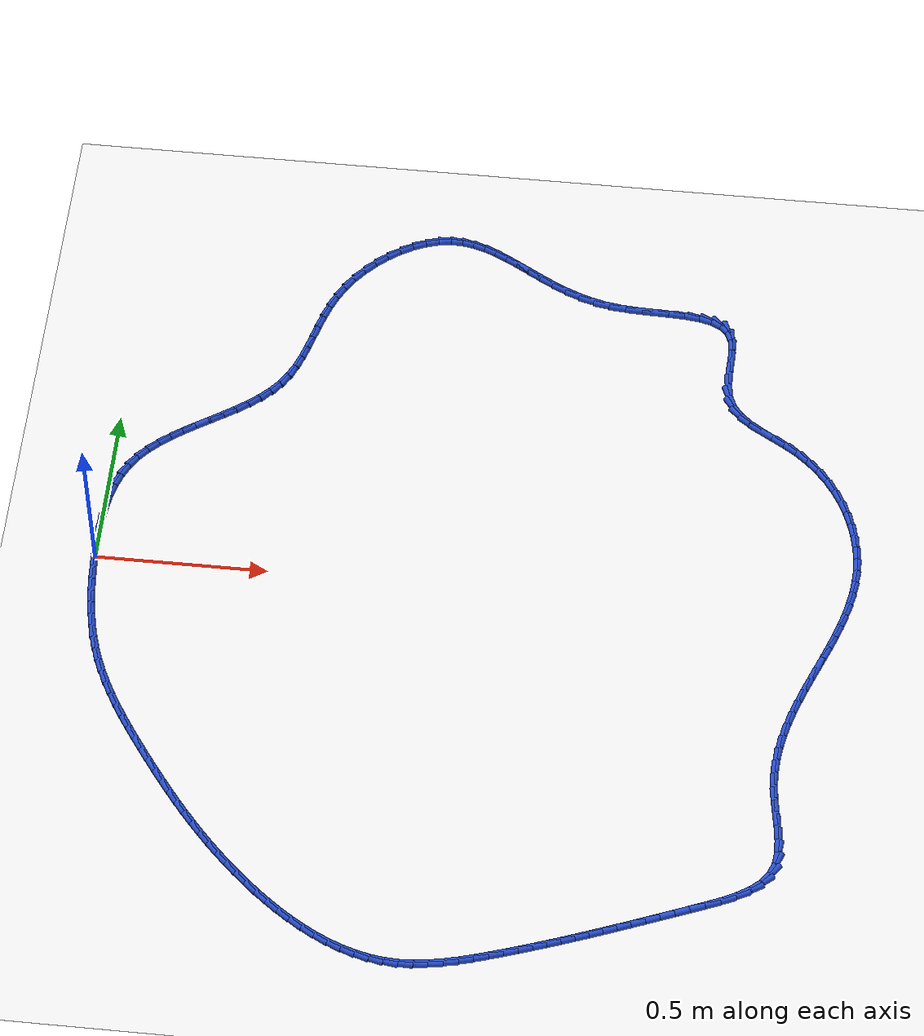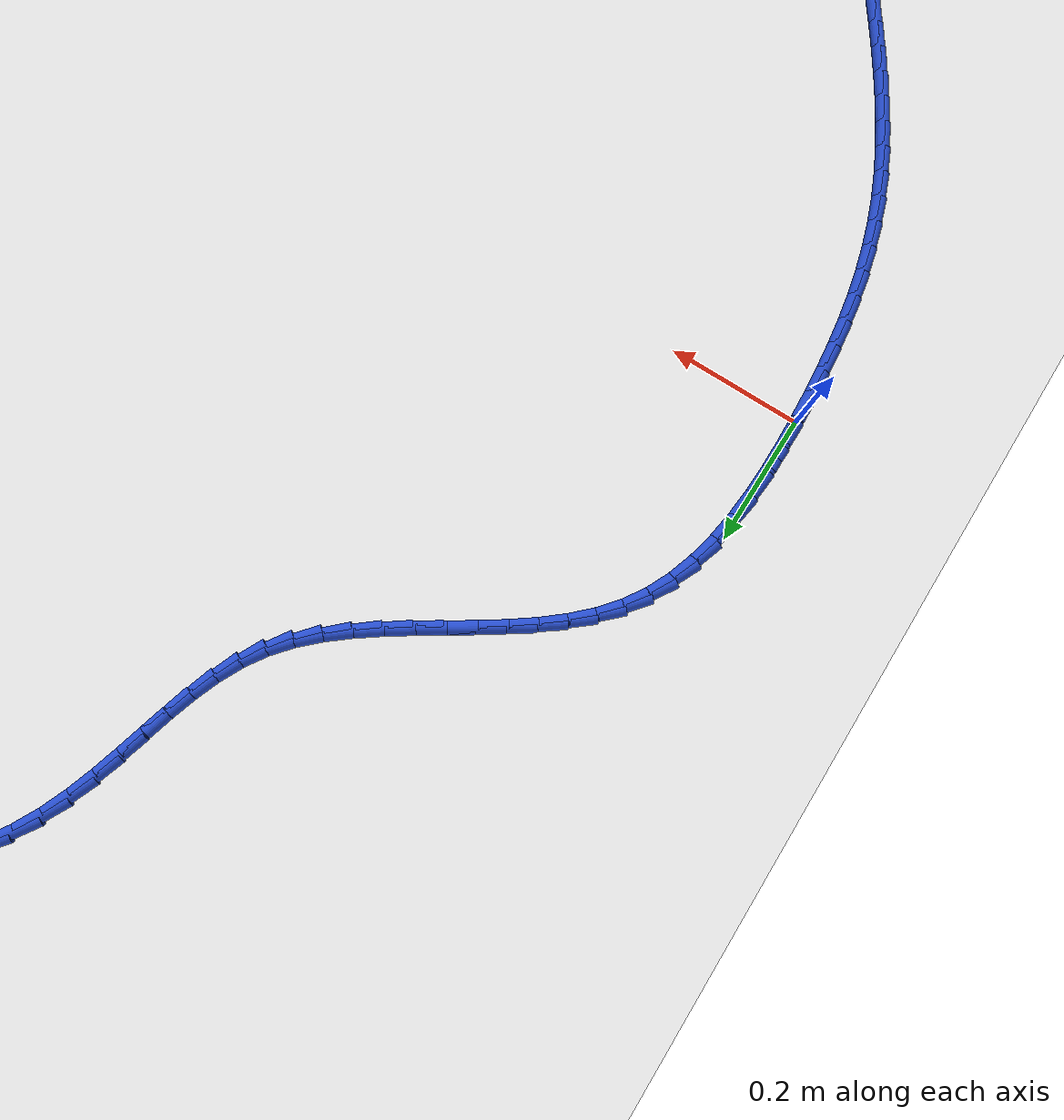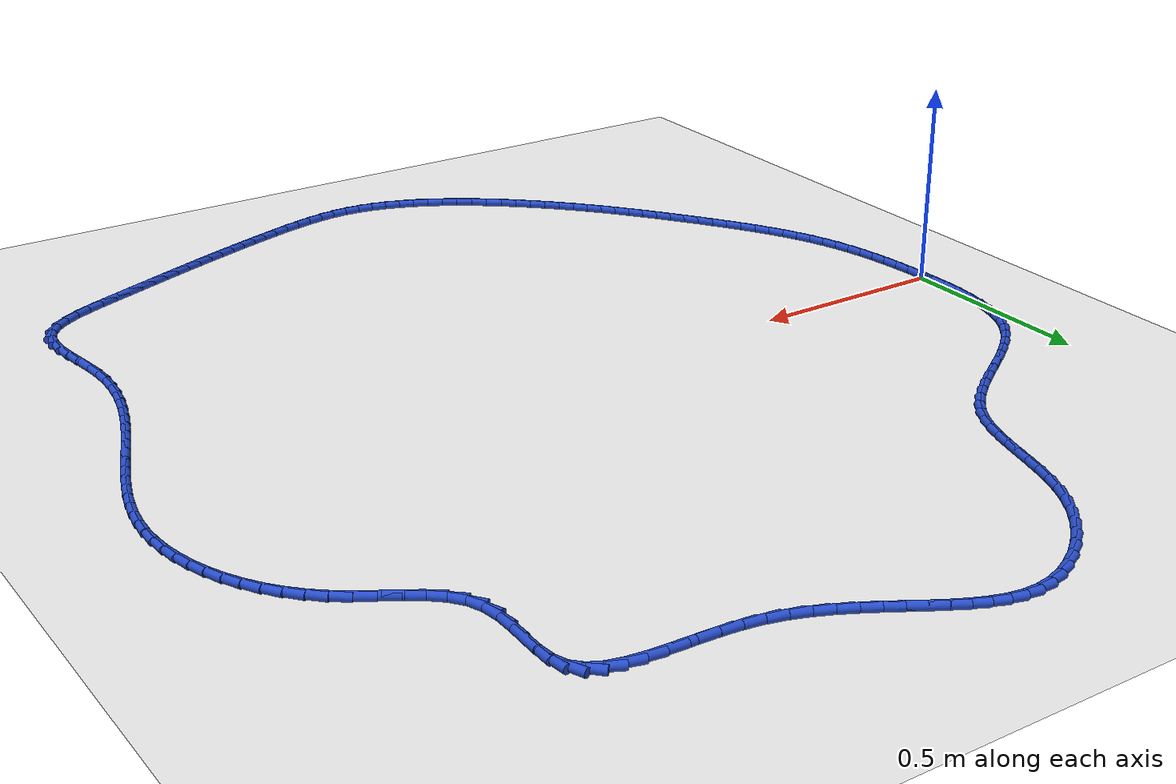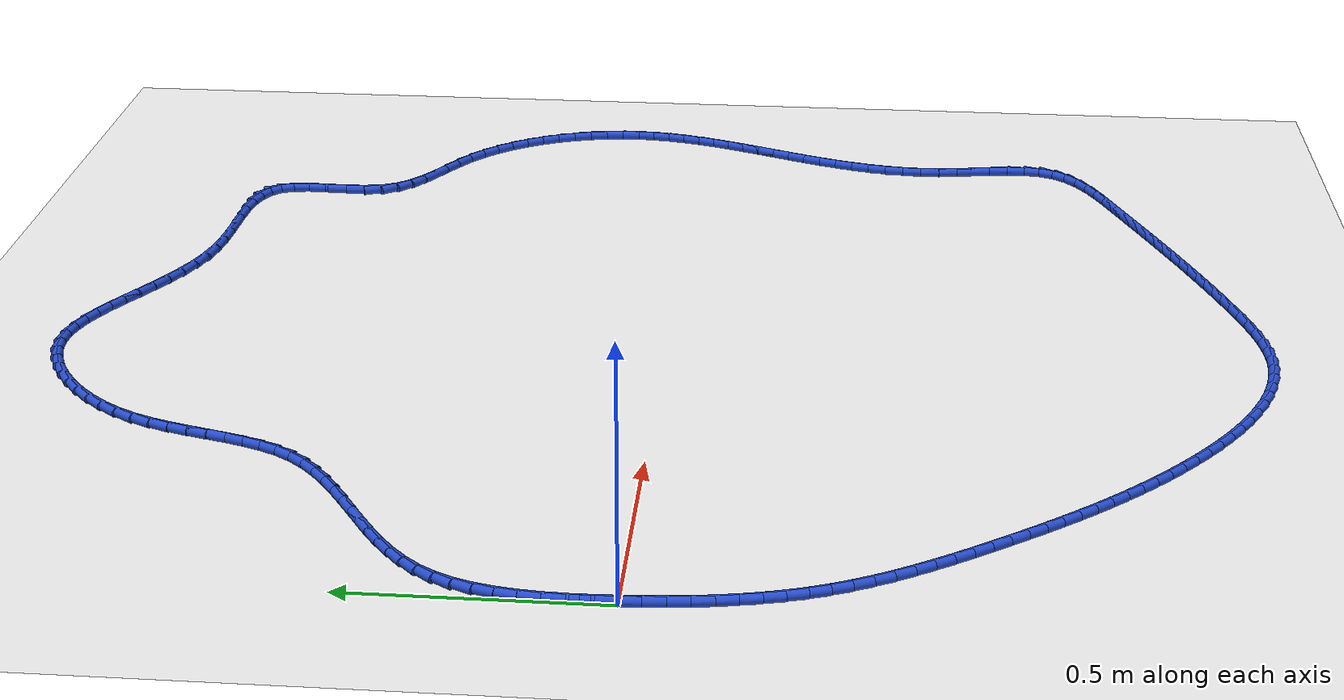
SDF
<sdf version="1.6">
 <world name="default">
  <light name="sun" type="directional">
   <pose>0 0 10 0 -0 0</pose>
   <diffuse>0.8 0.8 0.8 1</diffuse>
   <specular>0.2 0.2 0.2 1</specular>
   <attenuation>
    <range>1000</range>
    <constant>0.9</constant>
    <linear>0.01</linear>
    <quadratic>0.001</quadratic>
   </attenuation>
   <direction>-0.5 0.1 -0.9</direction>
  </light>
  <model name="ground_plane">
   <static>1</static>
   <link name="link">
    <collision name="collision">
     <geometry><plane><normal>0 0 1</normal><size>100 100</size></plane></geometry>
     <surface><friction><ode><mu>100</mu><mu2>50</mu2></ode></friction></surface>
    </collision>
    <visual name="visual">
     <cast_shadows>0</cast_shadows>
     <geometry><plane><normal>0 0 1</normal><size>100 100</size></plane></geometry>
     <material>
      <script><uri>file://media/materials/scripts/gazebo.material</uri><name>Gazebo/WhiteGlow</name></script>
     </material>
    </visual>
   </link>
  </model>
  <gravity>0 0 -9.8</gravity>
  <magnetic_field>6e-06 2.3e-05 -4.2e-05</magnetic_field>
  <atmosphere type="adiabatic"/>
  <physics name="default_physics" default="0" type="ode">
   <max_step_size>0.001</max_step_size>
   <real_time_factor>1</real_time_factor>
   <real_time_update_rate>1000</real_time_update_rate>
  </physics>
  <scene><ambient>0.4 0.4 0.4 1</ambient><background>0.7 0.7 0.7 1</background><shadows>1</shadows></scene>
  <spherical_coordinates>
   <surface_model>EARTH_WGS84</surface_model>
   <latitude_deg>0</latitude_deg>
   <longitude_deg>0</longitude_deg>
   <elevation>0</elevation>
   <heading_deg>0</heading_deg>
  </spherical_coordinates>
  <model name="line">
   <link name="link_0">
    <pose>3.371868756429919e-17 1.3877787807814457e-17 0.01 0 1.57 -1.5402129373418287</pose>
    <collision name="collision">
     <geometry><cylinder><radius>0.01</radius><length>0.08</length></cylinder></geometry>
    </collision>
    <visual name="visual">
     <material>
      <script><name>Gazebo/Blue</name><uri>file://media/materials/scripts/gazebo.material</uri></script>
     </material>
     <geometry><cylinder><radius>0.01</radius><length>0.08</length></cylinder></geometry>
    </visual>
   </link>
   <link name="link_1">
    <pose>-0.001301941402759294 0.04255693956164811 0.01 0 1.57 -1.5693150320624307</pose>
    <collision name="collision">
     <geometry><cylinder><radius>0.01</radius><length>0.08</length></cylinder></geometry>
    </collision>
    <visual name="visual">
     <material>
      <script><name>Gazebo/Blue</name><uri>file://media/materials/scripts/gazebo.material</uri></script>
     </material>
     <geometry><cylinder><radius>0.01</radius><length>0.08</length></cylinder></geometry>
    </visual>
   </link>
   <link name="link_2">
    <pose>-0.0013652244932487027 0.08527837967510893 0.01 0 1.57 1.5328641680909814</pose>
    <collision name="collision">
     <geometry><cylinder><radius>0.01</radius><length>0.08</length></cylinder></geometry>
    </collision>
    <visual name="visual">
     <material>
      <script><name>Gazebo/Blue</name><uri>file://media/materials/scripts/gazebo.material</uri></script>
     </material>
     <geometry><cylinder><radius>0.01</radius><length>0.08</length></cylinder></geometry>
    </visual>
   </link>
   <link name="link_3">
    <pose>0.00024713933660895594 0.12776450477019138 0.01 0 1.57 1.4820240221549235</pose>
    <collision name="collision">
     <geometry><cylinder><radius>0.01</radius><length>0.08</length></cylinder></geometry>
    </collision>
    <visual name="visual">
     <material>
      <script><name>Gazebo/Blue</name><uri>file://media/materials/scripts/gazebo.material</uri></script>
     </material>
     <geometry><cylinder><radius>0.01</radius><length>0.08</length></cylinder></geometry>
    </visual>
   </link>
   <link name="link_4">
    <pose>0.003972138694890834 0.16961549927670438 0.01 0 1.57 1.4182611296050296</pose>
    <collision name="collision">
     <geometry><cylinder><radius>0.01</radius><length>0.08</length></cylinder></geometry>
    </collision>
    <visual name="visual">
     <material>
      <script><name>Gazebo/Blue</name><uri>file://media/materials/scripts/gazebo.material</uri></script>
     </material>
     <geometry><cylinder><radius>0.01</radius><length>0.08</length></cylinder></geometry>
    </visual>
   </link>
   <link name="link_5">
    <pose>0.010246762189674083 0.21043154762445682 0.01 0 1.57 1.3398247356249542</pose>
    <collision name="collision">
     <geometry><cylinder><radius>0.01</radius><length>0.08</length></cylinder></geometry>
    </collision>
    <visual name="visual">
     <material>
      <script><name>Gazebo/Blue</name><uri>file://media/materials/scripts/gazebo.material</uri></script>
     </material>
     <geometry><cylinder><radius>0.01</radius><length>0.08</length></cylinder></geometry>
    </visual>
   </link>
   <link name="link_6">
    <pose>0.01950799842903584 0.2498128342432576 0.01 0 1.57 1.2449939007286595</pose>
    <collision name="collision">
     <geometry><cylinder><radius>0.01</radius><length>0.08</length></cylinder></geometry>
    </collision>
    <visual name="visual">
     <material>
      <script><name>Gazebo/Blue</name><uri>file://media/materials/scripts/gazebo.material</uri></script>
     </material>
     <geometry><cylinder><radius>0.01</radius><length>0.08</length></cylinder></geometry>
    </visual>
   </link>
   <link name="link_7">
    <pose>0.03219283602105327 0.28735954356291565 0.01 0 1.57 1.1326274270484658</pose>
    <collision name="collision">
     <geometry><cylinder><radius>0.01</radius><length>0.08</length></cylinder></geometry>
    </collision>
    <visual name="visual">
     <material>
      <script><name>Gazebo/Blue</name><uri>file://media/materials/scripts/gazebo.material</uri></script>
     </material>
     <geometry><cylinder><radius>0.01</radius><length>0.08</length></cylinder></geometry>
    </visual>
   </link>
   <link name="link_8">
    <pose>0.048738263573803536 0.3226718600132399 0.01 0 1.57 1.0034730099232079</pose>
    <collision name="collision">
     <geometry><cylinder><radius>0.01</radius><length>0.08</length></cylinder></geometry>
    </collision>
    <visual name="visual">
     <material>
      <script><name>Gazebo/Blue</name><uri>file://media/materials/scripts/gazebo.material</uri></script>
     </material>
     <geometry><cylinder><radius>0.01</radius><length>0.08</length></cylinder></geometry>
    </visual>
   </link>
   <link name="link_9">
    <pose>0.06956723937037929 0.35536021585902394 0.01 0 1.57 0.8757069126929217</pose>
    <collision name="collision">
     <geometry><cylinder><radius>0.01</radius><length>0.08</length></cylinder></geometry>
    </collision>
    <visual name="visual">
     <material>
      <script><name>Gazebo/Blue</name><uri>file://media/materials/scripts/gazebo.material</uri></script>
     </material>
     <geometry><cylinder><radius>0.01</radius><length>0.08</length></cylinder></geometry>
    </visual>
   </link>
   <link name="link_10">
    <pose>0.09461251286339317 0.3853930948862107 0.01 0 1.57 0.7712299344867344</pose>
    <collision name="collision">
     <geometry><cylinder><radius>0.01</radius><length>0.08</length></cylinder></geometry>
    </collision>
    <visual name="visual">
     <material>
      <script><name>Gazebo/Blue</name><uri>file://media/materials/scripts/gazebo.material</uri></script>
     </material>
     <geometry><cylinder><radius>0.01</radius><length>0.08</length></cylinder></geometry>
    </visual>
   </link>
   <link name="link_11">
    <pose>0.12320025709258224 0.41318202799417475 0.01 0 1.57 0.6910021167794856</pose>
    <collision name="collision">
     <geometry><cylinder><radius>0.01</radius><length>0.08</length></cylinder></geometry>
    </collision>
    <visual name="visual">
     <material>
      <script><name>Gazebo/Blue</name><uri>file://media/materials/scripts/gazebo.material</uri></script>
     </material>
     <geometry><cylinder><radius>0.01</radius><length>0.08</length></cylinder></geometry>
    </visual>
   </link>
   <link name="link_12">
    <pose>0.15461900975855827 0.439166035163647 0.01 0 1.57 0.6332014041513747</pose>
    <collision name="collision">
     <geometry><cylinder><radius>0.01</radius><length>0.08</length></cylinder></geometry>
    </collision>
    <visual name="visual">
     <material>
      <script><name>Gazebo/Blue</name><uri>file://media/materials/scripts/gazebo.material</uri></script>
     </material>
     <geometry><cylinder><radius>0.01</radius><length>0.08</length></cylinder></geometry>
    </visual>
   </link>
   <link name="link_13">
    <pose>0.1881573085619332 0.46378413637535887 0.01 0 1.57 0.5957600893504336</pose>
    <collision name="collision">
     <geometry><cylinder><radius>0.01</radius><length>0.08</length></cylinder></geometry>
    </collision>
    <visual name="visual">
     <material>
      <script><name>Gazebo/Blue</name><uri>file://media/materials/scripts/gazebo.material</uri></script>
     </material>
     <geometry><cylinder><radius>0.01</radius><length>0.08</length></cylinder></geometry>
    </visual>
   </link>
   <link name="link_14">
    <pose>0.2231036912033186 0.4874753516100416 0.01 0 1.57 0.5770730301367993</pose>
    <collision name="collision">
     <geometry><cylinder><radius>0.01</radius><length>0.08</length></cylinder></geometry>
    </collision>
    <visual name="visual">
     <material>
      <script><name>Gazebo/Blue</name><uri>file://media/materials/scripts/gazebo.material</uri></script>
     </material>
     <geometry><cylinder><radius>0.01</radius><length>0.08</length></cylinder></geometry>
    </visual>
   </link>
   <link name="link_15">
    <pose>0.25874669538332645 0.5106787008484259 0.01 0 1.57 0.5763001790471307</pose>
    <collision name="collision">
     <geometry><cylinder><radius>0.01</radius><length>0.08</length></cylinder></geometry>
    </collision>
    <visual name="visual">
     <material>
      <script><name>Gazebo/Blue</name><uri>file://media/materials/scripts/gazebo.material</uri></script>
     </material>
     <geometry><cylinder><radius>0.01</radius><length>0.08</length></cylinder></geometry>
    </visual>
   </link>
   <link name="link_16">
    <pose>0.2943748588025686 0.5338332040712436 0.01 0 1.57 0.5934724999072294</pose>
    <collision name="collision">
     <geometry><cylinder><radius>0.01</radius><length>0.08</length></cylinder></geometry>
    </collision>
    <visual name="visual">
     <material>
      <script><name>Gazebo/Blue</name><uri>file://media/materials/scripts/gazebo.material</uri></script>
     </material>
     <geometry><cylinder><radius>0.01</radius><length>0.08</length></cylinder></geometry>
    </visual>
   </link>
   <link name="link_17">
    <pose>0.32927671916165663 0.5573778812592254 0.01 0 1.57 0.6295063294615603</pose>
    <collision name="collision">
     <geometry><cylinder><radius>0.01</radius><length>0.08</length></cylinder></geometry>
    </collision>
    <visual name="visual">
     <material>
      <script><name>Gazebo/Blue</name><uri>file://media/materials/scripts/gazebo.material</uri></script>
     </material>
     <geometry><cylinder><radius>0.01</radius><length>0.08</length></cylinder></geometry>
    </visual>
   </link>
   <link name="link_18">
    <pose>0.3627408141612025 0.5817517523931025 0.01 0 1.57 0.6861278292938195</pose>
    <collision name="collision">
     <geometry><cylinder><radius>0.01</radius><length>0.08</length></cylinder></geometry>
    </collision>
    <visual name="visual">
     <material>
      <script><name>Gazebo/Blue</name><uri>file://media/materials/scripts/gazebo.material</uri></script>
     </material>
     <geometry><cylinder><radius>0.01</radius><length>0.08</length></cylinder></geometry>
    </visual>
   </link>
   <link name="link_19">
    <pose>0.3940556815018181 0.6073938374536062 0.01 0 1.57 0.7656016604716777</pose>
    <collision name="collision">
     <geometry><cylinder><radius>0.01</radius><length>0.08</length></cylinder></geometry>
    </collision>
    <visual name="visual">
     <material>
      <script><name>Gazebo/Blue</name><uri>file://media/materials/scripts/gazebo.material</uri></script>
     </material>
     <geometry><cylinder><radius>0.01</radius><length>0.08</length></cylinder></geometry>
    </visual>
   </link>
   <link name="link_20">
    <pose>0.42250985888411524 0.6347431564214678 0.01 0 1.57 0.8700382645957109</pose>
    <collision name="collision">
     <geometry><cylinder><radius>0.01</radius><length>0.08</length></cylinder></geometry>
    </collision>
    <visual name="visual">
     <material>
      <script><name>Gazebo/Blue</name><uri>file://media/materials/scripts/gazebo.material</uri></script>
     </material>
     <geometry><cylinder><radius>0.01</radius><length>0.08</length></cylinder></geometry>
    </visual>
   </link>
   <link name="link_21">
    <pose>0.4473918840087051 0.6642387292774177 0.01 0 1.57 0.9972930796232857</pose>
    <collision name="collision">
     <geometry><cylinder><radius>0.01</radius><length>0.08</length></cylinder></geometry>
    </collision>
    <visual name="visual">
     <material>
      <script><name>Gazebo/Blue</name><uri>file://media/materials/scripts/gazebo.material</uri></script>
     </material>
     <geometry><cylinder><radius>0.01</radius><length>0.08</length></cylinder></geometry>
    </visual>
   </link>
   <link name="link_22">
    <pose>0.4680821518128771 0.6962708644134924 0.01 0 1.57 1.1159063662617592</pose>
    <collision name="collision">
     <geometry><cylinder><radius>0.01</radius><length>0.08</length></cylinder></geometry>
    </collision>
    <visual name="visual">
     <material>
      <script><name>Gazebo/Blue</name><uri>file://media/materials/scripts/gazebo.material</uri></script>
     </material>
     <geometry><cylinder><radius>0.01</radius><length>0.08</length></cylinder></geometry>
    </visual>
   </link>
   <link name="link_23">
    <pose>0.48492944581038877 0.7307163369635842 0.01 0 1.57 1.205464749394915</pose>
    <collision name="collision">
     <geometry><cylinder><radius>0.01</radius><length>0.08</length></cylinder></geometry>
    </collision>
    <visual name="visual">
     <material>
      <script><name>Gazebo/Blue</name><uri>file://media/materials/scripts/gazebo.material</uri></script>
     </material>
     <geometry><cylinder><radius>0.01</radius><length>0.08</length></cylinder></geometry>
    </visual>
   </link>
   <link name="link_24">
    <pose>0.49886312130800875 0.7671440467606012 0.01 0 1.57 1.265749019838712</pose>
    <collision name="collision">
     <geometry><cylinder><radius>0.01</radius><length>0.08</length></cylinder></geometry>
    </collision>
    <visual name="visual">
     <material>
      <script><name>Gazebo/Blue</name><uri>file://media/materials/scripts/gazebo.material</uri></script>
     </material>
     <geometry><cylinder><radius>0.01</radius><length>0.08</length></cylinder></geometry>
    </visual>
   </link>
   <link name="link_25">
    <pose>0.5108204048673011 0.8051187195370761 0.01 0 1.57 1.2984060600359086</pose>
    <collision name="collision">
     <geometry><cylinder><radius>0.01</radius><length>0.08</length></cylinder></geometry>
    </collision>
    <visual name="visual">
     <material>
      <script><name>Gazebo/Blue</name><uri>file://media/materials/scripts/gazebo.material</uri></script>
     </material>
     <geometry><cylinder><radius>0.01</radius><length>0.08</length></cylinder></geometry>
    </visual>
   </link>
   <link name="link_26">
    <pose>0.5217385230498298 0.8442050810255421 0.01 0 1.57 1.3052048329932449</pose>
    <collision name="collision">
     <geometry><cylinder><radius>0.01</radius><length>0.08</length></cylinder></geometry>
    </collision>
    <visual name="visual">
     <material>
      <script><name>Gazebo/Blue</name><uri>file://media/materials/scripts/gazebo.material</uri></script>
     </material>
     <geometry><cylinder><radius>0.01</radius><length>0.08</length></cylinder></geometry>
    </visual>
   </link>
   <link name="link_27">
    <pose>0.5325547024171587 0.883967856958531 0.01 0 1.57 1.2873787360145554</pose>
    <collision name="collision">
     <geometry><cylinder><radius>0.01</radius><length>0.08</length></cylinder></geometry>
    </collision>
    <visual name="visual">
     <material>
      <script><name>Gazebo/Blue</name><uri>file://media/materials/scripts/gazebo.material</uri></script>
     </material>
     <geometry><cylinder><radius>0.01</radius><length>0.08</length></cylinder></geometry>
    </visual>
   </link>
   <link name="link_28">
    <pose>0.5442061695308522 0.9239717730685761 0.01 0 1.57 1.2455670459733883</pose>
    <collision name="collision">
     <geometry><cylinder><radius>0.01</radius><length>0.08</length></cylinder></geometry>
    </collision>
    <visual name="visual">
     <material>
      <script><name>Gazebo/Blue</name><uri>file://media/materials/scripts/gazebo.material</uri></script>
     </material>
     <geometry><cylinder><radius>0.01</radius><length>0.08</length></cylinder></geometry>
    </visual>
   </link>
   <link name="link_29">
    <pose>0.5576301509524737 0.96378155508821 0.01 0 1.57 1.180175594671434</pose>
    <collision name="collision">
     <geometry><cylinder><radius>0.01</radius><length>0.08</length></cylinder></geometry>
    </collision>
    <visual name="visual">
     <material>
      <script><name>Gazebo/Blue</name><uri>file://media/materials/scripts/gazebo.material</uri></script>
     </material>
     <geometry><cylinder><radius>0.01</radius><length>0.08</length></cylinder></geometry>
    </visual>
   </link>
   <link name="link_30">
    <pose>0.5737638732435874 1.0029619287499651 0.01 0 1.57 1.0921632405418389</pose>
    <collision name="collision">
     <geometry><cylinder><radius>0.01</radius><length>0.08</length></cylinder></geometry>
    </collision>
    <visual name="visual">
     <material>
      <script><name>Gazebo/Blue</name><uri>file://media/materials/scripts/gazebo.material</uri></script>
     </material>
     <geometry><cylinder><radius>0.01</radius><length>0.08</length></cylinder></geometry>
    </visual>
   </link>
   <link name="link_31">
    <pose>0.5935410301082394 1.0410774073641091 0.01 0 1.57 0.9924328100676605</pose>
    <collision name="collision">
     <geometry><cylinder><radius>0.01</radius><length>0.08</length></cylinder></geometry>
    </collision>
    <visual name="visual">
     <material>
      <script><name>Gazebo/Blue</name><uri>file://media/materials/scripts/gazebo.material</uri></script>
     </material>
     <geometry><cylinder><radius>0.01</radius><length>0.08</length></cylinder></geometry>
    </visual>
   </link>
   <link name="link_32">
    <pose>0.6174261201630655 1.0776642926635582 0.01 0 1.57 0.8979612889216475</pose>
    <collision name="collision">
     <geometry><cylinder><radius>0.01</radius><length>0.08</length></cylinder></geometry>
    </collision>
    <visual name="visual">
     <material>
      <script><name>Gazebo/Blue</name><uri>file://media/materials/scripts/gazebo.material</uri></script>
     </material>
     <geometry><cylinder><radius>0.01</radius><length>0.08</length></cylinder></geometry>
    </visual>
   </link>
   <link name="link_33">
    <pose>0.6449490473149506 1.1122026914387504 0.01 0 1.57 0.8075137057887503</pose>
    <collision name="collision">
     <geometry><cylinder><radius>0.01</radius><length>0.08</length></cylinder></geometry>
    </collision>
    <visual name="visual">
     <material>
      <script><name>Gazebo/Blue</name><uri>file://media/materials/scripts/gazebo.material</uri></script>
     </material>
     <geometry><cylinder><radius>0.01</radius><length>0.08</length></cylinder></geometry>
    </visual>
   </link>
   <link name="link_34">
    <pose>0.6755290045945821 1.1441660537001808 0.01 0 1.57 0.717760168533304</pose>
    <collision name="collision">
     <geometry><cylinder><radius>0.01</radius><length>0.08</length></cylinder></geometry>
    </collision>
    <visual name="visual">
     <material>
      <script><name>Gazebo/Blue</name><uri>file://media/materials/scripts/gazebo.material</uri></script>
     </material>
     <geometry><cylinder><radius>0.01</radius><length>0.08</length></cylinder></geometry>
    </visual>
   </link>
   <link name="link_35">
    <pose>0.7085851850326469 1.1730278294583452 0.01 0 1.57 0.625312395822167</pose>
    <collision name="collision">
     <geometry><cylinder><radius>0.01</radius><length>0.08</length></cylinder></geometry>
    </collision>
    <visual name="visual">
     <material>
      <script><name>Gazebo/Blue</name><uri>file://media/materials/scripts/gazebo.material</uri></script>
     </material>
     <geometry><cylinder><radius>0.01</radius><length>0.08</length></cylinder></geometry>
    </visual>
   </link>
   <link name="link_36">
    <pose>0.7435367816598317 1.198261468723738 0.01 0 1.57 0.5265025715095883</pose>
    <collision name="collision">
     <geometry><cylinder><radius>0.01</radius><length>0.08</length></cylinder></geometry>
    </collision>
    <visual name="visual">
     <material>
      <script><name>Gazebo/Blue</name><uri>file://media/materials/scripts/gazebo.material</uri></script>
     </material>
     <geometry><cylinder><radius>0.01</radius><length>0.08</length></cylinder></geometry>
    </visual>
   </link>
   <link name="link_37">
    <pose>0.7798029875068235 1.2193404215068544 0.01 0 1.57 0.4171691489627002</pose>
    <collision name="collision">
     <geometry><cylinder><radius>0.01</radius><length>0.08</length></cylinder></geometry>
    </collision>
    <visual name="visual">
     <material>
      <script><name>Gazebo/Blue</name><uri>file://media/materials/scripts/gazebo.material</uri></script>
     </material>
     <geometry><cylinder><radius>0.01</radius><length>0.08</length></cylinder></geometry>
    </visual>
   </link>
   <link name="link_38">
    <pose>0.8168029956043089 1.2357381378181895 0.01 0 1.57 0.29254365792671816</pose>
    <collision name="collision">
     <geometry><cylinder><radius>0.01</radius><length>0.08</length></cylinder></geometry>
    </collision>
    <visual name="visual">
     <material>
      <script><name>Gazebo/Blue</name><uri>file://media/materials/scripts/gazebo.material</uri></script>
     </material>
     <geometry><cylinder><radius>0.01</radius><length>0.08</length></cylinder></geometry>
    </visual>
   </link>
   <link name="link_39">
    <pose>0.8539559989829751 1.2469280676682382 0.01 0 1.57 0.14747331689437954</pose>
    <collision name="collision">
     <geometry><cylinder><radius>0.01</radius><length>0.08</length></cylinder></geometry>
    </collision>
    <visual name="visual">
     <material>
      <script><name>Gazebo/Blue</name><uri>file://media/materials/scripts/gazebo.material</uri></script>
     </material>
     <geometry><cylinder><radius>0.01</radius><length>0.08</length></cylinder></geometry>
    </visual>
   </link>
   <link name="link_40">
    <pose>0.8906811906735093 1.2523836610674959 0.01 0 1.57 -0.016351206418530283</pose>
    <collision name="collision">
     <geometry><cylinder><radius>0.01</radius><length>0.08</length></cylinder></geometry>
    </collision>
    <visual name="visual">
     <material>
      <script><name>Gazebo/Blue</name><uri>file://media/materials/scripts/gazebo.material</uri></script>
     </material>
     <geometry><cylinder><radius>0.01</radius><length>0.08</length></cylinder></geometry>
    </visual>
   </link>
   <link name="link_41">
    <pose>0.9265363697001605 1.2517973333792214 0.01 0 1.57 -0.17012788651870434</pose>
    <collision name="collision">
     <geometry><cylinder><radius>0.01</radius><length>0.08</length></cylinder></geometry>
    </collision>
    <visual name="visual">
     <material>
      <script><name>Gazebo/Blue</name><uri>file://media/materials/scripts/gazebo.material</uri></script>
     </material>
     <geometry><cylinder><radius>0.01</radius><length>0.08</length></cylinder></geometry>
    </visual>
   </link>
   <link name="link_42">
    <pose>0.9616512548317919 1.2457650006408687 0.01 0 1.57 -0.2981648159815667</pose>
    <collision name="collision">
     <geometry><cylinder><radius>0.01</radius><length>0.08</length></cylinder></geometry>
    </collision>
    <visual name="visual">
     <material>
      <script><name>Gazebo/Blue</name><uri>file://media/materials/scripts/gazebo.material</uri></script>
     </material>
     <geometry><cylinder><radius>0.01</radius><length>0.08</length></cylinder></geometry>
    </visual>
   </link>
   <link name="link_43">
    <pose>0.9963030558633342 1.235115580535222 0.01 0 1.57 -0.3966879468717914</pose>
    <collision name="collision">
     <geometry><cylinder><radius>0.01</radius><length>0.08</length></cylinder></geometry>
    </collision>
    <visual name="visual">
     <material>
      <script><name>Gazebo/Blue</name><uri>file://media/materials/scripts/gazebo.material</uri></script>
     </material>
     <geometry><cylinder><radius>0.01</radius><length>0.08</length></cylinder></geometry>
    </visual>
   </link>
   <link name="link_44">
    <pose>1.03076898274853 1.2206779909959502 0.01 0 1.57 -0.46638041518679646</pose>
    <collision name="collision">
     <geometry><cylinder><radius>0.01</radius><length>0.08</length></cylinder></geometry>
    </collision>
    <visual name="visual">
     <material>
      <script><name>Gazebo/Blue</name><uri>file://media/materials/scripts/gazebo.material</uri></script>
     </material>
     <geometry><cylinder><radius>0.01</radius><length>0.08</length></cylinder></geometry>
    </visual>
   </link>
   <link name="link_45">
    <pose>1.065326245441121 1.2032811499567206 0.01 0 1.57 -0.5098063022087665</pose>
    <collision name="collision">
     <geometry><cylinder><radius>0.01</radius><length>0.08</length></cylinder></geometry>
    </collision>
    <visual name="visual">
     <material>
      <script><name>Gazebo/Blue</name><uri>file://media/materials/scripts/gazebo.material</uri></script>
     </material>
     <geometry><cylinder><radius>0.01</radius><length>0.08</length></cylinder></geometry>
    </visual>
   </link>
   <link name="link_46">
    <pose>1.1002520538948501 1.1837539753512023 0.01 0 1.57 -0.5297196386514679</pose>
    <collision name="collision">
     <geometry><cylinder><radius>0.01</radius><length>0.08</length></cylinder></geometry>
    </collision>
    <visual name="visual">
     <material>
      <script><name>Gazebo/Blue</name><uri>file://media/materials/scripts/gazebo.material</uri></script>
     </material>
     <geometry><cylinder><radius>0.01</radius><length>0.08</length></cylinder></geometry>
    </visual>
   </link>
   <link name="link_47">
    <pose>1.1358236180634598 1.162925385113064 0.01 0 1.57 -0.5283322602829534</pose>
    <collision name="collision">
     <geometry><cylinder><radius>0.01</radius><length>0.08</length></cylinder></geometry>
    </collision>
    <visual name="visual">
     <material>
      <script><name>Gazebo/Blue</name><uri>file://media/materials/scripts/gazebo.material</uri></script>
     </material>
     <geometry><cylinder><radius>0.01</radius><length>0.08</length></cylinder></geometry>
    </visual>
   </link>
   <link name="link_48">
    <pose>1.1723181479006914 1.1416242971759734 0.01 0 1.57 -0.5071626566063893</pose>
    <collision name="collision">
     <geometry><cylinder><radius>0.01</radius><length>0.08</length></cylinder></geometry>
    </collision>
    <visual name="visual">
     <material>
      <script><name>Gazebo/Blue</name><uri>file://media/materials/scripts/gazebo.material</uri></script>
     </material>
     <geometry><cylinder><radius>0.01</radius><length>0.08</length></cylinder></geometry>
    </visual>
   </link>
   <link name="link_49">
    <pose>1.2100128533602879 1.120679629473599 0.01 0 1.57 -0.4671802714398391</pose>
    <collision name="collision">
     <geometry><cylinder><radius>0.01</radius><length>0.08</length></cylinder></geometry>
    </collision>
    <visual name="visual">
     <material>
      <script><name>Gazebo/Blue</name><uri>file://media/materials/scripts/gazebo.material</uri></script>
     </material>
     <geometry><cylinder><radius>0.01</radius><length>0.08</length></cylinder></geometry>
    </visual>
   </link>
   <link name="link_50">
    <pose>1.2491849443959908 1.1009202999396097 0.01 0 1.57 -0.40911714017227935</pose>
    <collision name="collision">
     <geometry><cylinder><radius>0.01</radius><length>0.08</length></cylinder></geometry>
    </collision>
    <visual name="visual">
     <material>
      <script><name>Gazebo/Blue</name><uri>file://media/materials/scripts/gazebo.material</uri></script>
     </material>
     <geometry><cylinder><radius>0.01</radius><length>0.08</length></cylinder></geometry>
    </visual>
   </link>
   <link name="link_51">
    <pose>1.2901116309615432 1.0831752265076737 0.01 0 1.57 -0.3339021195107667</pose>
    <collision name="collision">
     <geometry><cylinder><radius>0.01</radius><length>0.08</length></cylinder></geometry>
    </collision>
    <visual name="visual">
     <material>
      <script><name>Gazebo/Blue</name><uri>file://media/materials/scripts/gazebo.material</uri></script>
     </material>
     <geometry><cylinder><radius>0.01</radius><length>0.08</length></cylinder></geometry>
    </visual>
   </link>
   <link name="link_52">
    <pose>1.3330701230106872 1.0682733271114588 0.01 0 1.57 -0.2431675466790465</pose>
    <collision name="collision">
     <geometry><cylinder><radius>0.01</radius><length>0.08</length></cylinder></geometry>
    </collision>
    <visual name="visual">
     <material>
      <script><name>Gazebo/Blue</name><uri>file://media/materials/scripts/gazebo.material</uri></script>
     </material>
     <geometry><cylinder><radius>0.01</radius><length>0.08</length></cylinder></geometry>
    </visual>
   </link>
   <link name="link_53">
    <pose>1.3783376304971646 1.0570435196846342 0.01 0 1.57 -0.1456776935267775</pose>
    <collision name="collision">
     <geometry><cylinder><radius>0.01</radius><length>0.08</length></cylinder></geometry>
    </collision>
    <visual name="visual">
     <material>
      <script><name>Gazebo/Blue</name><uri>file://media/materials/scripts/gazebo.material</uri></script>
     </material>
     <geometry><cylinder><radius>0.01</radius><length>0.08</length></cylinder></geometry>
    </visual>
   </link>
   <link name="link_54">
    <pose>1.42600359173215 1.0500501109070908 0.01 0 1.57 -0.07510812287152586</pose>
    <collision name="collision">
     <geometry><cylinder><radius>0.01</radius><length>0.08</length></cylinder></geometry>
    </collision>
    <visual name="visual">
     <material>
      <script><name>Gazebo/Blue</name><uri>file://media/materials/scripts/gazebo.material</uri></script>
     </material>
     <geometry><cylinder><radius>0.01</radius><length>0.08</length></cylinder></geometry>
    </visual>
   </link>
   <link name="link_55">
    <pose>1.4750921760559546 1.0463562108236164 0.01 0 1.57 -0.03781792178557751</pose>
    <collision name="collision">
     <geometry><cylinder><radius>0.01</radius><length>0.08</length></cylinder></geometry>
    </collision>
    <visual name="visual">
     <material>
      <script><name>Gazebo/Blue</name><uri>file://media/materials/scripts/gazebo.material</uri></script>
     </material>
     <geometry><cylinder><radius>0.01</radius><length>0.08</length></cylinder></geometry>
    </visual>
   </link>
   <link name="link_56">
    <pose>1.5242523511176602 1.0444961883518673 0.01 0 1.57 -0.031158605753219992</pose>
    <collision name="collision">
     <geometry><cylinder><radius>0.01</radius><length>0.08</length></cylinder></geometry>
    </collision>
    <visual name="visual">
     <material>
      <script><name>Gazebo/Blue</name><uri>file://media/materials/scripts/gazebo.material</uri></script>
     </material>
     <geometry><cylinder><radius>0.01</radius><length>0.08</length></cylinder></geometry>
    </visual>
   </link>
   <link name="link_57">
    <pose>1.5721326652700809 1.0430038215294792 0.01 0 1.57 -0.05719699922522653</pose>
    <collision name="collision">
     <geometry><cylinder><radius>0.01</radius><length>0.08</length></cylinder></geometry>
    </collision>
    <visual name="visual">
     <material>
      <script><name>Gazebo/Blue</name><uri>file://media/materials/scripts/gazebo.material</uri></script>
     </material>
     <geometry><cylinder><radius>0.01</radius><length>0.08</length></cylinder></geometry>
    </visual>
   </link>
   <link name="link_58">
    <pose>1.6173816668660306 1.0404128883940884 0.01 0 1.57 -0.12429395373571693</pose>
    <collision name="collision">
     <geometry><cylinder><radius>0.01</radius><length>0.08</length></cylinder></geometry>
    </collision>
    <visual name="visual">
     <material>
      <script><name>Gazebo/Blue</name><uri>file://media/materials/scripts/gazebo.material</uri></script>
     </material>
     <geometry><cylinder><radius>0.01</radius><length>0.08</length></cylinder></geometry>
    </visual>
   </link>
   <link name="link_59">
    <pose>1.6586479042583213 1.0352571669833315 0.01 0 1.57 -0.2503077564738116</pose>
    <collision name="collision">
     <geometry><cylinder><radius>0.01</radius><length>0.08</length></cylinder></geometry>
    </collision>
    <visual name="visual">
     <material>
      <script><name>Gazebo/Blue</name><uri>file://media/materials/scripts/gazebo.material</uri></script>
     </material>
     <geometry><cylinder><radius>0.01</radius><length>0.08</length></cylinder></geometry>
    </visual>
   </link>
   <link name="link_60">
    <pose>1.694579925799767 1.0260704353348438 0.01 0 1.57 -0.4653089791982063</pose>
    <collision name="collision">
     <geometry><cylinder><radius>0.01</radius><length>0.08</length></cylinder></geometry>
    </collision>
    <visual name="visual">
     <material>
      <script><name>Gazebo/Blue</name><uri>file://media/materials/scripts/gazebo.material</uri></script>
     </material>
     <geometry><cylinder><radius>0.01</radius><length>0.08</length></cylinder></geometry>
    </visual>
   </link>
   <link name="link_61">
    <pose>1.7238262798431796 1.0113864714862613 0.01 0 1.57 -0.7956221966597491</pose>
    <collision name="collision">
     <geometry><cylinder><radius>0.01</radius><length>0.08</length></cylinder></geometry>
    </collision>
    <visual name="visual">
     <material>
      <script><name>Gazebo/Blue</name><uri>file://media/materials/scripts/gazebo.material</uri></script>
     </material>
     <geometry><cylinder><radius>0.01</radius><length>0.08</length></cylinder></geometry>
    </visual>
   </link>
   <link name="link_62">
    <pose>1.7450355147413734 0.9897390534752208 0.01 0 1.57 -1.1890866099172082</pose>
    <collision name="collision">
     <geometry><cylinder><radius>0.01</radius><length>0.08</length></cylinder></geometry>
    </collision>
    <visual name="visual">
     <material>
      <script><name>Gazebo/Blue</name><uri>file://media/materials/scripts/gazebo.material</uri></script>
     </material>
     <geometry><cylinder><radius>0.01</radius><length>0.08</length></cylinder></geometry>
    </visual>
   </link>
   <link name="link_63">
    <pose>1.7570431057543732 0.9598245185783914 0.01 0 1.57 -1.458287280915823</pose>
    <collision name="collision">
     <geometry><cylinder><radius>0.01</radius><length>0.08</length></cylinder></geometry>
    </collision>
    <visual name="visual">
     <material>
      <script><name>Gazebo/Blue</name><uri>file://media/materials/scripts/gazebo.material</uri></script>
     </material>
     <geometry><cylinder><radius>0.01</radius><length>0.08</length></cylinder></geometry>
    </visual>
   </link>
   <link name="link_64">
    <pose>1.761252116343009 0.9225720831710116 0.01 0 1.57 1.5631584580072675</pose>
    <collision name="collision">
     <geometry><cylinder><radius>0.01</radius><length>0.08</length></cylinder></geometry>
    </collision>
    <visual name="visual">
     <material>
      <script><name>Gazebo/Blue</name><uri>file://media/materials/scripts/gazebo.material</uri></script>
     </material>
     <geometry><cylinder><radius>0.01</radius><length>0.08</length></cylinder></geometry>
    </visual>
   </link>
   <link name="link_65">
    <pose>1.7609310226433266 0.8805332023391028 0.01 0 1.57 1.5359814922940118</pose>
    <collision name="collision">
     <geometry><cylinder><radius>0.01</radius><length>0.08</length></cylinder></geometry>
    </collision>
    <visual name="visual">
     <material>
      <script><name>Gazebo/Blue</name><uri>file://media/materials/scripts/gazebo.material</uri></script>
     </material>
     <geometry><cylinder><radius>0.01</radius><length>0.08</length></cylinder></geometry>
    </visual>
   </link>
   <link name="link_66">
    <pose>1.7593902836904989 0.8362958412048084 0.01 0 1.57 -1.5582519113877884</pose>
    <collision name="collision">
     <geometry><cylinder><radius>0.01</radius><length>0.08</length></cylinder></geometry>
    </collision>
    <visual name="visual">
     <material>
      <script><name>Gazebo/Blue</name><uri>file://media/materials/scripts/gazebo.material</uri></script>
     </material>
     <geometry><cylinder><radius>0.01</radius><length>0.08</length></cylinder></geometry>
    </visual>
   </link>
   <link name="link_67">
    <pose>1.7599403585197013 0.792447964890274 0.01 0 1.57 -1.4261976096504339</pose>
    <collision name="collision">
     <geometry><cylinder><radius>0.01</radius><length>0.08</length></cylinder></geometry>
    </collision>
    <visual name="visual">
     <material>
      <script><name>Gazebo/Blue</name><uri>file://media/materials/scripts/gazebo.material</uri></script>
     </material>
     <geometry><cylinder><radius>0.01</radius><length>0.08</length></cylinder></geometry>
    </visual>
   </link>
   <link name="link_68">
    <pose>1.765891706166107 0.7515775385176438 0.01 0 1.57 -1.184262760017396</pose>
    <collision name="collision">
     <geometry><cylinder><radius>0.01</radius><length>0.08</length></cylinder></geometry>
    </collision>
    <visual name="visual">
     <material>
      <script><name>Gazebo/Blue</name><uri>file://media/materials/scripts/gazebo.material</uri></script>
     </material>
     <geometry><cylinder><radius>0.01</radius><length>0.08</length></cylinder></geometry>
    </visual>
   </link>
   <link name="link_69">
    <pose>1.7803311577837029 0.7161005132148716 0.01 0 1.57 -0.9146831074800857</pose>
    <collision name="collision">
     <geometry><cylinder><radius>0.01</radius><length>0.08</length></cylinder></geometry>
    </collision>
    <visual name="visual">
     <material>
      <script><name>Gazebo/Blue</name><uri>file://media/materials/scripts/gazebo.material</uri></script>
     </material>
     <geometry><cylinder><radius>0.01</radius><length>0.08</length></cylinder></geometry>
    </visual>
   </link>
   <link name="link_70">
    <pose>1.8033853889689875 0.6861558960268942 0.01 0 1.57 -0.7168910019843812</pose>
    <collision name="collision">
     <geometry><cylinder><radius>0.01</radius><length>0.08</length></cylinder></geometry>
    </collision>
    <visual name="visual">
     <material>
      <script><name>Gazebo/Blue</name><uri>file://media/materials/scripts/gazebo.material</uri></script>
     </material>
     <geometry><cylinder><radius>0.01</radius><length>0.08</length></cylinder></geometry>
    </visual>
   </link>
   <link name="link_71">
    <pose>1.8330849048905153 0.6602703250672801 0.01 0 1.57 -0.5969566195680475</pose>
    <collision name="collision">
     <geometry><cylinder><radius>0.01</radius><length>0.08</length></cylinder></geometry>
    </collision>
    <visual name="visual">
     <material>
      <script><name>Gazebo/Blue</name><uri>file://media/materials/scripts/gazebo.material</uri></script>
     </material>
     <geometry><cylinder><radius>0.01</radius><length>0.08</length></cylinder></geometry>
    </visual>
   </link>
   <link name="link_72">
    <pose>1.8674158580069635 0.6369363224586118 0.01 0 1.57 -0.542819743999252</pose>
    <collision name="collision">
     <geometry><cylinder><radius>0.01</radius><length>0.08</length></cylinder></geometry>
    </collision>
    <visual name="visual">
     <material>
      <script><name>Gazebo/Blue</name><uri>file://media/materials/scripts/gazebo.material</uri></script>
     </material>
     <geometry><cylinder><radius>0.01</radius><length>0.08</length></cylinder></geometry>
    </visual>
   </link>
   <link name="link_73">
    <pose>1.9043644007770093 0.6146464103234709 0.01 0 1.57 -0.5447536552811245</pose>
    <collision name="collision">
     <geometry><cylinder><radius>0.01</radius><length>0.08</length></cylinder></geometry>
    </collision>
    <visual name="visual">
     <material>
      <script><name>Gazebo/Blue</name><uri>file://media/materials/scripts/gazebo.material</uri></script>
     </material>
     <geometry><cylinder><radius>0.01</radius><length>0.08</length></cylinder></geometry>
    </visual>
   </link>
   <link name="link_74">
    <pose>1.9419166856593302 0.5918931107844391 0.01 0 1.57 -0.5998844561634533</pose>
    <collision name="collision">
     <geometry><cylinder><radius>0.01</radius><length>0.08</length></cylinder></geometry>
    </collision>
    <visual name="visual">
     <material>
      <script><name>Gazebo/Blue</name><uri>file://media/materials/scripts/gazebo.material</uri></script>
     </material>
     <geometry><cylinder><radius>0.01</radius><length>0.08</length></cylinder></geometry>
    </visual>
   </link>
   <link name="link_75">
    <pose>1.9780614013407571 0.5671713108625649 0.01 0 1.57 -0.6936888601320007</pose>
    <collision name="collision">
     <geometry><cylinder><radius>0.01</radius><length>0.08</length></cylinder></geometry>
    </collision>
    <visual name="visual">
     <material>
      <script><name>Gazebo/Blue</name><uri>file://media/materials/scripts/gazebo.material</uri></script>
     </material>
     <geometry><cylinder><radius>0.01</radius><length>0.08</length></cylinder></geometry>
    </visual>
   </link>
   <link name="link_76">
    <pose>2.011343939112425 0.5394949932812612 0.01 0 1.57 -0.7892312715022529</pose>
    <collision name="collision">
     <geometry><cylinder><radius>0.01</radius><length>0.08</length></cylinder></geometry>
    </collision>
    <visual name="visual">
     <material>
      <script><name>Gazebo/Blue</name><uri>file://media/materials/scripts/gazebo.material</uri></script>
     </material>
     <geometry><cylinder><radius>0.01</radius><length>0.08</length></cylinder></geometry>
    </visual>
   </link>
   <link name="link_77">
    <pose>2.041561241494025 0.5090451460177544 0.01 0 1.57 -0.8811543210112385</pose>
    <collision name="collision">
     <geometry><cylinder><radius>0.01</radius><length>0.08</length></cylinder></geometry>
    </collision>
    <visual name="visual">
     <material>
      <script><name>Gazebo/Blue</name><uri>file://media/materials/scripts/gazebo.material</uri></script>
     </material>
     <geometry><cylinder><radius>0.01</radius><length>0.08</length></cylinder></geometry>
    </visual>
   </link>
   <link name="link_78">
    <pose>2.068681072211994 0.476162038779966 0.01 0 1.57 -0.9695959242122205</pose>
    <collision name="collision">
     <geometry><cylinder><radius>0.01</radius><length>0.08</length></cylinder></geometry>
    </collision>
    <visual name="visual">
     <material>
      <script><name>Gazebo/Blue</name><uri>file://media/materials/scripts/gazebo.material</uri></script>
     </material>
     <geometry><cylinder><radius>0.01</radius><length>0.08</length></cylinder></geometry>
    </visual>
   </link>
   <link name="link_79">
    <pose>2.0926711949927723 0.441185941275816 0.01 0 1.57 -1.0549344981326458</pose>
    <collision name="collision">
     <geometry><cylinder><radius>0.01</radius><length>0.08</length></cylinder></geometry>
    </collision>
    <visual name="visual">
     <material>
      <script><name>Gazebo/Blue</name><uri>file://media/materials/scripts/gazebo.material</uri></script>
     </material>
     <geometry><cylinder><radius>0.01</radius><length>0.08</length></cylinder></geometry>
    </visual>
   </link>
   <link name="link_80">
    <pose>2.113499373562797 0.40445712321322436 0.01 0 1.57 -1.137733074092599</pose>
    <collision name="collision">
     <geometry><cylinder><radius>0.01</radius><length>0.08</length></cylinder></geometry>
    </collision>
    <visual name="visual">
     <material>
      <script><name>Gazebo/Blue</name><uri>file://media/materials/scripts/gazebo.material</uri></script>
     </material>
     <geometry><cylinder><radius>0.01</radius><length>0.08</length></cylinder></geometry>
    </visual>
   </link>
   <link name="link_81">
    <pose>2.1311333716485055 0.36631585430011204 0.01 0 1.57 -1.218692683642936</pose>
    <collision name="collision">
     <geometry><cylinder><radius>0.01</radius><length>0.08</length></cylinder></geometry>
    </collision>
    <visual name="visual">
     <material>
      <script><name>Gazebo/Blue</name><uri>file://media/materials/scripts/gazebo.material</uri></script>
     </material>
     <geometry><cylinder><radius>0.01</radius><length>0.08</length></cylinder></geometry>
    </visual>
   </link>
   <link name="link_82">
    <pose>2.1455409529763365 0.32710240424439935 0.01 0 1.57 -1.2986182564822601</pose>
    <collision name="collision">
     <geometry><cylinder><radius>0.01</radius><length>0.08</length></cylinder></geometry>
    </collision>
    <visual name="visual">
     <material>
      <script><name>Gazebo/Blue</name><uri>file://media/materials/scripts/gazebo.material</uri></script>
     </material>
     <geometry><cylinder><radius>0.01</radius><length>0.08</length></cylinder></geometry>
    </visual>
   </link>
   <link name="link_83">
    <pose>2.1566898812727264 0.28715704275400605 0.01 0 1.57 -1.3783963968486297</pose>
    <collision name="collision">
     <geometry><cylinder><radius>0.01</radius><length>0.08</length></cylinder></geometry>
    </collision>
    <visual name="visual">
     <material>
      <script><name>Gazebo/Blue</name><uri>file://media/materials/scripts/gazebo.material</uri></script>
     </material>
     <geometry><cylinder><radius>0.01</radius><length>0.08</length></cylinder></geometry>
    </visual>
   </link>
   <link name="link_84">
    <pose>2.1645479202641145 0.2468200395368534 0.01 0 1.57 -1.4589820125764221</pose>
    <collision name="collision">
     <geometry><cylinder><radius>0.01</radius><length>0.08</length></cylinder></geometry>
    </collision>
    <visual name="visual">
     <material>
      <script><name>Gazebo/Blue</name><uri>file://media/materials/scripts/gazebo.material</uri></script>
     </material>
     <geometry><cylinder><radius>0.01</radius><length>0.08</length></cylinder></geometry>
    </visual>
   </link>
   <link name="link_85">
    <pose>2.1690828336769385 0.20643166430086088 0.01 0 1.57 -1.5413742203764105</pose>
    <collision name="collision">
     <geometry><cylinder><radius>0.01</radius><length>0.08</length></cylinder></geometry>
    </collision>
    <visual name="visual">
     <material>
      <script><name>Gazebo/Blue</name><uri>file://media/materials/scripts/gazebo.material</uri></script>
     </material>
     <geometry><cylinder><radius>0.01</radius><length>0.08</length></cylinder></geometry>
    </visual>
   </link>
   <link name="link_86">
    <pose>2.1702630043756845 0.16633153958562433 0.01 0 1.57 1.5180313942333072</pose>
    <collision name="collision">
     <geometry><cylinder><radius>0.01</radius><length>0.08</length></cylinder></geometry>
    </collision>
    <visual name="visual">
     <material>
      <script><name>Gazebo/Blue</name><uri>file://media/materials/scripts/gazebo.material</uri></script>
     </material>
     <geometry><cylinder><radius>0.01</radius><length>0.08</length></cylinder></geometry>
    </visual>
   </link>
   <link name="link_87">
    <pose>2.168171961959467 0.1267389281505984 0.01 0 1.57 1.4429576533127935</pose>
    <collision name="collision">
     <geometry><cylinder><radius>0.01</radius><length>0.08</length></cylinder></geometry>
    </collision>
    <visual name="visual">
     <material>
      <script><name>Gazebo/Blue</name><uri>file://media/materials/scripts/gazebo.material</uri></script>
     </material>
     <geometry><cylinder><radius>0.01</radius><length>0.08</length></cylinder></geometry>
    </visual>
   </link>
   <link name="link_88">
    <pose>2.1631426494627157 0.08761238760943799 0.01 0 1.57 1.3770070553616547</pose>
    <collision name="collision">
     <geometry><cylinder><radius>0.01</radius><length>0.08</length></cylinder></geometry>
    </collision>
    <visual name="visual">
     <material>
      <script><name>Gazebo/Blue</name><uri>file://media/materials/scripts/gazebo.material</uri></script>
     </material>
     <geometry><cylinder><radius>0.01</radius><length>0.08</length></cylinder></geometry>
    </visual>
   </link>
   <link name="link_89">
    <pose>2.1555406254746177 0.04887638341494148 0.01 0 1.57 1.3208284747273251</pose>
    <collision name="collision">
     <geometry><cylinder><radius>0.01</radius><length>0.08</length></cylinder></geometry>
    </collision>
    <visual name="visual">
     <material>
      <script><name>Gazebo/Blue</name><uri>file://media/materials/scripts/gazebo.material</uri></script>
     </material>
     <geometry><cylinder><radius>0.01</radius><length>0.08</length></cylinder></geometry>
    </visual>
   </link>
   <link name="link_90">
    <pose>2.1457314485843564 0.010455381019906073 0.01 0 1.57 1.2746292530645242</pose>
    <collision name="collision">
     <geometry><cylinder><radius>0.01</radius><length>0.08</length></cylinder></geometry>
    </collision>
    <visual name="visual">
     <material>
      <script><name>Gazebo/Blue</name><uri>file://media/materials/scripts/gazebo.material</uri></script>
     </material>
     <geometry><cylinder><radius>0.01</radius><length>0.08</length></cylinder></geometry>
    </visual>
   </link>
   <link name="link_91">
    <pose>2.1340806773811165 -0.027726154122870675 0.01 0 1.57 1.2383304844749423</pose>
    <collision name="collision">
     <geometry><cylinder><radius>0.01</radius><length>0.08</length></cylinder></geometry>
    </collision>
    <visual name="visual">
     <material>
      <script><name>Gazebo/Blue</name><uri>file://media/materials/scripts/gazebo.material</uri></script>
     </material>
     <geometry><cylinder><radius>0.01</radius><length>0.08</length></cylinder></geometry>
    </visual>
   </link>
   <link name="link_92">
    <pose>2.120953870454084 -0.06574375656059198 0.01 0 1.57 1.211705965371024</pose>
    <collision name="collision">
     <geometry><cylinder><radius>0.01</radius><length>0.08</length></cylinder></geometry>
    </collision>
    <visual name="visual">
     <material>
      <script><name>Gazebo/Blue</name><uri>file://media/materials/scripts/gazebo.material</uri></script>
     </material>
     <geometry><cylinder><radius>0.01</radius><length>0.08</length></cylinder></geometry>
    </visual>
   </link>
   <link name="link_93">
    <pose>2.106716586392442 -0.10367296084045868 0.01 0 1.57 1.1944879876017243</pose>
    <collision name="collision">
     <geometry><cylinder><radius>0.01</radius><length>0.08</length></cylinder></geometry>
    </collision>
    <visual name="visual">
     <material>
      <script><name>Gazebo/Blue</name><uri>file://media/materials/scripts/gazebo.material</uri></script>
     </material>
     <geometry><cylinder><radius>0.01</radius><length>0.08</length></cylinder></geometry>
    </visual>
   </link>
   <link name="link_94">
    <pose>2.091734383785376 -0.14158930150967414 0.01 0 1.57 1.1864381121315333</pose>
    <collision name="collision">
     <geometry><cylinder><radius>0.01</radius><length>0.08</length></cylinder></geometry>
    </collision>
    <visual name="visual">
     <material>
      <script><name>Gazebo/Blue</name><uri>file://media/materials/scripts/gazebo.material</uri></script>
     </material>
     <geometry><cylinder><radius>0.01</radius><length>0.08</length></cylinder></geometry>
    </visual>
   </link>
   <link name="link_95">
    <pose>2.076372821222071 -0.1795683131154407 0.01 0 1.57 1.1873876594602482</pose>
    <collision name="collision">
     <geometry><cylinder><radius>0.01</radius><length>0.08</length></cylinder></geometry>
    </collision>
    <visual name="visual">
     <material>
      <script><name>Gazebo/Blue</name><uri>file://media/materials/scripts/gazebo.material</uri></script>
     </material>
     <geometry><cylinder><radius>0.01</radius><length>0.08</length></cylinder></geometry>
    </visual>
   </link>
   <link name="link_96">
    <pose>2.0609974572917102 -0.2176855302049607 0.01 0 1.57 1.197253602473335</pose>
    <collision name="collision">
     <geometry><cylinder><radius>0.01</radius><length>0.08</length></cylinder></geometry>
    </collision>
    <visual name="visual">
     <material>
      <script><name>Gazebo/Blue</name><uri>file://media/materials/scripts/gazebo.material</uri></script>
     </material>
     <geometry><cylinder><radius>0.01</radius><length>0.08</length></cylinder></geometry>
    </visual>
   </link>
   <link name="link_97">
    <pose>2.0459738505834797 -0.25601648732543675 0.01 0 1.57 1.2160337202314928</pose>
    <collision name="collision">
     <geometry><cylinder><radius>0.01</radius><length>0.08</length></cylinder></geometry>
    </collision>
    <visual name="visual">
     <material>
      <script><name>Gazebo/Blue</name><uri>file://media/materials/scripts/gazebo.material</uri></script>
     </material>
     <geometry><cylinder><radius>0.01</radius><length>0.08</length></cylinder></geometry>
    </visual>
   </link>
   <link name="link_98">
    <pose>2.0316675596865643 -0.29463671902407196 0.01 0 1.57 1.2437822140363244</pose>
    <collision name="collision">
     <geometry><cylinder><radius>0.01</radius><length>0.08</length></cylinder></geometry>
    </collision>
    <visual name="visual">
     <material>
      <script><name>Gazebo/Blue</name><uri>file://media/materials/scripts/gazebo.material</uri></script>
     </material>
     <geometry><cylinder><radius>0.01</radius><length>0.08</length></cylinder></geometry>
    </visual>
   </link>
   <link name="link_99">
    <pose>2.0184441431901474 -0.3336217598480673 0.01 0 1.57 1.2805647281705805</pose>
    <collision name="collision">
     <geometry><cylinder><radius>0.01</radius><length>0.08</length></cylinder></geometry>
    </collision>
    <visual name="visual">
     <material>
      <script><name>Gazebo/Blue</name><uri>file://media/materials/scripts/gazebo.material</uri></script>
     </material>
     <geometry><cylinder><radius>0.01</radius><length>0.08</length></cylinder></geometry>
    </visual>
   </link>
   <link name="link_100">
    <pose>2.0066691596834154 -0.3730471443446259 0.01 0 1.57 1.3263909109588448</pose>
    <collision name="collision">
     <geometry><cylinder><radius>0.01</radius><length>0.08</length></cylinder></geometry>
    </collision>
    <visual name="visual">
     <material>
      <script><name>Gazebo/Blue</name><uri>file://media/materials/scripts/gazebo.material</uri></script>
     </material>
     <geometry><cylinder><radius>0.01</radius><length>0.08</length></cylinder></geometry>
    </visual>
   </link>
   <link name="link_101">
    <pose>1.9967081677555516 -0.4129884070609501 0.01 0 1.57 1.3811245701106807</pose>
    <collision name="collision">
     <geometry><cylinder><radius>0.01</radius><length>0.08</length></cylinder></geometry>
    </collision>
    <visual name="visual">
     <material>
      <script><name>Gazebo/Blue</name><uri>file://media/materials/scripts/gazebo.material</uri></script>
     </material>
     <geometry><cylinder><radius>0.01</radius><length>0.08</length></cylinder></geometry>
    </visual>
   </link>
   <link name="link_102">
    <pose>1.9889267259957415 -0.4535210825442426 0.01 0 1.57 1.4443774986622042</pose>
    <collision name="collision">
     <geometry><cylinder><radius>0.01</radius><length>0.08</length></cylinder></geometry>
    </collision>
    <visual name="visual">
     <material>
      <script><name>Gazebo/Blue</name><uri>file://media/materials/scripts/gazebo.material</uri></script>
     </material>
     <geometry><cylinder><radius>0.01</radius><length>0.08</length></cylinder></geometry>
    </visual>
   </link>
   <link name="link_103">
    <pose>1.9836903929931688 -0.49472070534170653 0.01 0 1.57 1.5154036245181026</pose>
    <collision name="collision">
     <geometry><cylinder><radius>0.01</radius><length>0.08</length></cylinder></geometry>
    </collision>
    <visual name="visual">
     <material>
      <script><name>Gazebo/Blue</name><uri>file://media/materials/scripts/gazebo.material</uri></script>
     </material>
     <geometry><cylinder><radius>0.01</radius><length>0.08</length></cylinder></geometry>
    </visual>
   </link>
   <link name="link_104">
    <pose>1.9813647273370198 -0.5366628100005427 0.01 0 1.57 -1.5485699223589675</pose>
    <collision name="collision">
     <geometry><cylinder><radius>0.01</radius><length>0.08</length></cylinder></geometry>
    </collision>
    <visual name="visual">
     <material>
      <script><name>Gazebo/Blue</name><uri>file://media/materials/scripts/gazebo.material</uri></script>
     </material>
     <geometry><cylinder><radius>0.01</radius><length>0.08</length></cylinder></geometry>
    </visual>
   </link>
   <link name="link_105">
    <pose>1.9823152876164778 -0.5794229310679543 0.01 0 1.57 -1.4692684135198342</pose>
    <collision name="collision">
     <geometry><cylinder><radius>0.01</radius><length>0.08</length></cylinder></geometry>
    </collision>
    <visual name="visual">
     <material>
      <script><name>Gazebo/Blue</name><uri>file://media/materials/scripts/gazebo.material</uri></script>
     </material>
     <geometry><cylinder><radius>0.01</radius><length>0.08</length></cylinder></geometry>
    </visual>
   </link>
   <link name="link_106">
    <pose>1.9867568690926722 -0.6230199053817219 0.01 0 1.57 -1.4192274223718309</pose>
    <collision name="collision">
     <geometry><cylinder><radius>0.01</radius><length>0.08</length></cylinder></geometry>
    </collision>
    <visual name="visual">
     <material>
      <script><name>Gazebo/Blue</name><uri>file://media/materials/scripts/gazebo.material</uri></script>
     </material>
     <geometry><cylinder><radius>0.01</radius><length>0.08</length></cylinder></geometry>
    </visual>
   </link>
   <link name="link_107">
    <pose>1.9934638446135415 -0.6669308687407771 0.01 0 1.57 -1.4120789591819367</pose>
    <collision name="collision">
     <geometry><cylinder><radius>0.01</radius><length>0.08</length></cylinder></geometry>
    </collision>
    <visual name="visual">
     <material>
      <script><name>Gazebo/Blue</name><uri>file://media/materials/scripts/gazebo.material</uri></script>
     </material>
     <geometry><cylinder><radius>0.01</radius><length>0.08</length></cylinder></geometry>
    </visual>
   </link>
   <link name="link_108">
    <pose>2.0004108201597997 -0.7103321878510102 0.01 0 1.57 -1.4489016328538504</pose>
    <collision name="collision">
     <geometry><cylinder><radius>0.01</radius><length>0.08</length></cylinder></geometry>
    </collision>
    <visual name="visual">
     <material>
      <script><name>Gazebo/Blue</name><uri>file://media/materials/scripts/gazebo.material</uri></script>
     </material>
     <geometry><cylinder><radius>0.01</radius><length>0.08</length></cylinder></geometry>
    </visual>
   </link>
   <link name="link_109">
    <pose>2.005563846092502 -0.7523970118982192 0.01 0 1.57 -1.5375985631639986</pose>
    <collision name="collision">
     <geometry><cylinder><radius>0.01</radius><length>0.08</length></cylinder></geometry>
    </collision>
    <visual name="visual">
     <material>
      <script><name>Gazebo/Blue</name><uri>file://media/materials/scripts/gazebo.material</uri></script>
     </material>
     <geometry><cylinder><radius>0.01</radius><length>0.08</length></cylinder></geometry>
    </visual>
   </link>
   <link name="link_110">
    <pose>2.006888972772704 -0.7922984900681993 0.01 0 1.57 1.4485008631408987</pose>
    <collision name="collision">
     <geometry><cylinder><radius>0.01</radius><length>0.08</length></cylinder></geometry>
    </collision>
    <visual name="visual">
     <material>
      <script><name>Gazebo/Blue</name><uri>file://media/materials/scripts/gazebo.material</uri></script>
     </material>
     <geometry><cylinder><radius>0.01</radius><length>0.08</length></cylinder></geometry>
    </visual>
   </link>
   <link name="link_111">
    <pose>2.0023522505614606 -0.8292097715467485 0.01 0 1.57 1.2114675073227494</pose>
    <collision name="collision">
     <geometry><cylinder><radius>0.01</radius><length>0.08</length></cylinder></geometry>
    </collision>
    <visual name="visual">
     <material>
      <script><name>Gazebo/Blue</name><uri>file://media/materials/scripts/gazebo.material</uri></script>
     </material>
     <geometry><cylinder><radius>0.01</radius><length>0.08</length></cylinder></geometry>
    </visual>
   </link>
   <link name="link_112">
    <pose>1.9899206959633937 -0.8623043871846986 0.01 0 1.57 0.9301847891553994</pose>
    <collision name="collision">
     <geometry><cylinder><radius>0.01</radius><length>0.08</length></cylinder></geometry>
    </collision>
    <visual name="visual">
     <material>
      <script><name>Gazebo/Blue</name><uri>file://media/materials/scripts/gazebo.material</uri></script>
     </material>
     <geometry><cylinder><radius>0.01</radius><length>0.08</length></cylinder></geometry>
    </visual>
   </link>
   <link name="link_113">
    <pose>1.9684488802916482 -0.8911064871908686 0.01 0 1.57 0.7098999909946858</pose>
    <collision name="collision">
     <geometry><cylinder><radius>0.01</radius><length>0.08</length></cylinder></geometry>
    </collision>
    <visual name="visual">
     <material>
      <script><name>Gazebo/Blue</name><uri>file://media/materials/scripts/gazebo.material</uri></script>
     </material>
     <geometry><cylinder><radius>0.01</radius><length>0.08</length></cylinder></geometry>
    </visual>
   </link>
   <link name="link_114">
    <pose>1.9393195223623818 -0.9161389403274461 0.01 0 1.57 0.5609447326898488</pose>
    <collision name="collision">
     <geometry><cylinder><radius>0.01</radius><length>0.08</length></cylinder></geometry>
    </collision>
    <visual name="visual">
     <material>
      <script><name>Gazebo/Blue</name><uri>file://media/materials/scripts/gazebo.material</uri></script>
     </material>
     <geometry><cylinder><radius>0.01</radius><length>0.08</length></cylinder></geometry>
    </visual>
   </link>
   <link name="link_115">
    <pose>1.904362501635708 -0.9381012615495019 0.01 0 1.57 0.4659922342857898</pose>
    <collision name="collision">
     <geometry><cylinder><radius>0.01</radius><length>0.08</length></cylinder></geometry>
    </collision>
    <visual name="visual">
     <material>
      <script><name>Gazebo/Blue</name><uri>file://media/materials/scripts/gazebo.material</uri></script>
     </material>
     <geometry><cylinder><radius>0.01</radius><length>0.08</length></cylinder></geometry>
    </visual>
   </link>
   <link name="link_116">
    <pose>1.8654076975717462 -0.9576929658121078 0.01 0 1.57 0.4109688947495014</pose>
    <collision name="collision">
     <geometry><cylinder><radius>0.01</radius><length>0.08</length></cylinder></geometry>
    </collision>
    <visual name="visual">
     <material>
      <script><name>Gazebo/Blue</name><uri>file://media/materials/scripts/gazebo.material</uri></script>
     </material>
     <geometry><cylinder><radius>0.01</radius><length>0.08</length></cylinder></geometry>
    </visual>
   </link>
   <link name="link_117">
    <pose>1.824284989630612 -0.9756135680703358 0.01 0 1.57 0.3880115513879608</pose>
    <collision name="collision">
     <geometry><cylinder><radius>0.01</radius><length>0.08</length></cylinder></geometry>
    </collision>
    <visual name="visual">
     <material>
      <script><name>Gazebo/Blue</name><uri>file://media/materials/scripts/gazebo.material</uri></script>
     </material>
     <geometry><cylinder><radius>0.01</radius><length>0.08</length></cylinder></geometry>
    </visual>
   </link>
   <link name="link_118">
    <pose>1.7828207322628855 -0.9925613527245738 0.01 0 1.57 0.38574813438547984</pose>
    <collision name="collision">
     <geometry><cylinder><radius>0.01</radius><length>0.08</length></cylinder></geometry>
    </collision>
    <visual name="visual">
     <material>
      <script><name>Gazebo/Blue</name><uri>file://media/materials/scripts/gazebo.material</uri></script>
     </material>
     <geometry><cylinder><radius>0.01</radius><length>0.08</length></cylinder></geometry>
    </visual>
   </link>
   <link name="link_119">
    <pose>1.7422614691175449 -1.0090321965248734 0.01 0 1.57 0.3851317537875677</pose>
    <collision name="collision">
     <geometry><cylinder><radius>0.01</radius><length>0.08</length></cylinder></geometry>
    </collision>
    <visual name="visual">
     <material>
      <script><name>Gazebo/Blue</name><uri>file://media/materials/scripts/gazebo.material</uri></script>
     </material>
     <geometry><cylinder><radius>0.01</radius><length>0.08</length></cylinder></geometry>
    </visual>
   </link>
   <link name="link_120">
    <pose>1.702634034188182 -1.0250961846272755 0.01 0 1.57 0.38370498329851666</pose>
    <collision name="collision">
     <geometry><cylinder><radius>0.01</radius><length>0.08</length></cylinder></geometry>
    </collision>
    <visual name="visual">
     <material>
      <script><name>Gazebo/Blue</name><uri>file://media/materials/scripts/gazebo.material</uri></script>
     </material>
     <geometry><cylinder><radius>0.01</radius><length>0.08</length></cylinder></geometry>
    </visual>
   </link>
   <link name="link_121">
    <pose>1.6638111076134576 -1.0407695882204349 0.01 0 1.57 0.3814279784587061</pose>
    <collision name="collision">
     <geometry><cylinder><radius>0.01</radius><length>0.08</length></cylinder></geometry>
    </collision>
    <visual name="visual">
     <material>
      <script><name>Gazebo/Blue</name><uri>file://media/materials/scripts/gazebo.material</uri></script>
     </material>
     <geometry><cylinder><radius>0.01</radius><length>0.08</length></cylinder></geometry>
    </visual>
   </link>
   <link name="link_122">
    <pose>1.6256653695320291 -1.0560686784930062 0.01 0 1.57 0.3782733184342171</pose>
    <collision name="collision">
     <geometry><cylinder><radius>0.01</radius><length>0.08</length></cylinder></geometry>
    </collision>
    <visual name="visual">
     <material>
      <script><name>Gazebo/Blue</name><uri>file://media/materials/scripts/gazebo.material</uri></script>
     </material>
     <geometry><cylinder><radius>0.01</radius><length>0.08</length></cylinder></geometry>
    </visual>
   </link>
   <link name="link_123">
    <pose>1.588069500082556 -1.0710097266336445 0.01 0 1.57 0.3742281047790739</pose>
    <collision name="collision">
     <geometry><cylinder><radius>0.01</radius><length>0.08</length></cylinder></geometry>
    </collision>
    <visual name="visual">
     <material>
      <script><name>Gazebo/Blue</name><uri>file://media/materials/scripts/gazebo.material</uri></script>
     </material>
     <geometry><cylinder><radius>0.01</radius><length>0.08</length></cylinder></geometry>
    </visual>
   </link>
   <link name="link_124">
    <pose>1.550896179403696 -1.0856090038310044 0.01 0 1.57 0.3692956201876306</pose>
    <collision name="collision">
     <geometry><cylinder><radius>0.01</radius><length>0.08</length></cylinder></geometry>
    </collision>
    <visual name="visual">
     <material>
      <script><name>Gazebo/Blue</name><uri>file://media/materials/scripts/gazebo.material</uri></script>
     </material>
     <geometry><cylinder><radius>0.01</radius><length>0.08</length></cylinder></geometry>
    </visual>
   </link>
   <link name="link_125">
    <pose>1.5140180876341085 -1.099882781273741 0.01 0 1.57 0.36349638145788077</pose>
    <collision name="collision">
     <geometry><cylinder><radius>0.01</radius><length>0.08</length></cylinder></geometry>
    </collision>
    <visual name="visual">
     <material>
      <script><name>Gazebo/Blue</name><uri>file://media/materials/scripts/gazebo.material</uri></script>
     </material>
     <geometry><cylinder><radius>0.01</radius><length>0.08</length></cylinder></geometry>
    </visual>
   </link>
   <link name="link_126">
    <pose>1.4773079049124522 -1.1138473301505096 0.01 0 1.57 0.356868451334257</pose>
    <collision name="collision">
     <geometry><cylinder><radius>0.01</radius><length>0.08</length></cylinder></geometry>
    </collision>
    <visual name="visual">
     <material>
      <script><name>Gazebo/Blue</name><uri>file://media/materials/scripts/gazebo.material</uri></script>
     </material>
     <geometry><cylinder><radius>0.01</radius><length>0.08</length></cylinder></geometry>
    </visual>
   </link>
   <link name="link_127">
    <pose>1.4406383113773862 -1.1275189216499641 0.01 0 1.57 0.34946692429463516</pose>
    <collision name="collision">
     <geometry><cylinder><radius>0.01</radius><length>0.08</length></cylinder></geometry>
    </collision>
    <visual name="visual">
     <material>
      <script><name>Gazebo/Blue</name><uri>file://media/materials/scripts/gazebo.material</uri></script>
     </material>
     <geometry><cylinder><radius>0.01</radius><length>0.08</length></cylinder></geometry>
    </visual>
   </link>
   <link name="link_128">
    <pose>1.4038819871675692 -1.14091382696076 0.01 0 1.57 0.3413625675999758</pose>
    <collision name="collision">
     <geometry><cylinder><radius>0.01</radius><length>0.08</length></cylinder></geometry>
    </collision>
    <visual name="visual">
     <material>
      <script><name>Gazebo/Blue</name><uri>file://media/materials/scripts/gazebo.material</uri></script>
     </material>
     <geometry><cylinder><radius>0.01</radius><length>0.08</length></cylinder></geometry>
    </visual>
   </link>
   <link name="link_129">
    <pose>1.3669116124216592 -1.1540483172715512 0.01 0 1.57 0.33263967350492996</pose>
    <collision name="collision">
     <geometry><cylinder><radius>0.01</radius><length>0.08</length></cylinder></geometry>
    </collision>
    <visual name="visual">
     <material>
      <script><name>Gazebo/Blue</name><uri>file://media/materials/scripts/gazebo.material</uri></script>
     </material>
     <geometry><cylinder><radius>0.01</radius><length>0.08</length></cylinder></geometry>
    </visual>
   </link>
   <link name="link_130">
    <pose>1.329599867278315 -1.1669386637709929 0.01 0 1.57 0.32339325147928405</pose>
    <collision name="collision">
     <geometry><cylinder><radius>0.01</radius><length>0.08</length></cylinder></geometry>
    </collision>
    <visual name="visual">
     <material>
      <script><name>Gazebo/Blue</name><uri>file://media/materials/scripts/gazebo.material</uri></script>
     </material>
     <geometry><cylinder><radius>0.01</radius><length>0.08</length></cylinder></geometry>
    </visual>
   </link>
   <link name="link_131">
    <pose>1.2918194318761955 -1.179601137647741 0.01 0 1.57 0.31370454048131646</pose>
    <collision name="collision">
     <geometry><cylinder><radius>0.01</radius><length>0.08</length></cylinder></geometry>
    </collision>
    <visual name="visual">
     <material>
      <script><name>Gazebo/Blue</name><uri>file://media/materials/scripts/gazebo.material</uri></script>
     </material>
     <geometry><cylinder><radius>0.01</radius><length>0.08</length></cylinder></geometry>
    </visual>
   </link>
   <link name="link_132">
    <pose>1.2534434926502795 -1.1920509462204516 0.01 0 1.57 0.3001900015144924</pose>
    <collision name="collision">
     <geometry><cylinder><radius>0.01</radius><length>0.08</length></cylinder></geometry>
    </collision>
    <visual name="visual">
     <material>
      <script><name>Gazebo/Blue</name><uri>file://media/materials/scripts/gazebo.material</uri></script>
     </material>
     <geometry><cylinder><radius>0.01</radius><length>0.08</length></cylinder></geometry>
    </visual>
   </link>
   <link name="link_133">
    <pose>1.2144287877184656 -1.2041277313820766 0.01 0 1.57 0.27553980308165105</pose>
    <collision name="collision">
     <geometry><cylinder><radius>0.01</radius><length>0.08</length></cylinder></geometry>
    </collision>
    <visual name="visual">
     <material>
      <script><name>Gazebo/Blue</name><uri>file://media/materials/scripts/gazebo.material</uri></script>
     </material>
     <geometry><cylinder><radius>0.01</radius><length>0.08</length></cylinder></geometry>
    </visual>
   </link>
   <link name="link_134">
    <pose>1.1749079580259814 -1.2153015140474832 0.01 0 1.57 0.23850117631805287</pose>
    <collision name="collision">
     <geometry><cylinder><radius>0.01</radius><length>0.08</length></cylinder></geometry>
    </collision>
    <visual name="visual">
     <material>
      <script><name>Gazebo/Blue</name><uri>file://media/materials/scripts/gazebo.material</uri></script>
     </material>
     <geometry><cylinder><radius>0.01</radius><length>0.08</length></cylinder></geometry>
    </visual>
   </link>
   <link name="link_135">
    <pose>1.135035896992423 -1.2249955564667343 0.01 0 1.57 0.18835368286440227</pose>
    <collision name="collision">
     <geometry><cylinder><radius>0.01</radius><length>0.08</length></cylinder></geometry>
    </collision>
    <visual name="visual">
     <material>
      <script><name>Gazebo/Blue</name><uri>file://media/materials/scripts/gazebo.material</uri></script>
     </material>
     <geometry><cylinder><radius>0.01</radius><length>0.08</length></cylinder></geometry>
    </visual>
   </link>
   <link name="link_136">
    <pose>1.0949674980373876 -1.2326331208898942 0.01 0 1.57 0.12412468484557429</pose>
    <collision name="collision">
     <geometry><cylinder><radius>0.01</radius><length>0.08</length></cylinder></geometry>
    </collision>
    <visual name="visual">
     <material>
      <script><name>Gazebo/Blue</name><uri>file://media/materials/scripts/gazebo.material</uri></script>
     </material>
     <geometry><cylinder><radius>0.01</radius><length>0.08</length></cylinder></geometry>
    </visual>
   </link>
   <link name="link_137">
    <pose>1.0548576545804693 -1.2376374695670258 0.01 0 1.57 0.044833859428588925</pose>
    <collision name="collision">
     <geometry><cylinder><radius>0.01</radius><length>0.08</length></cylinder></geometry>
    </collision>
    <visual name="visual">
     <material>
      <script><name>Gazebo/Blue</name><uri>file://media/materials/scripts/gazebo.material</uri></script>
     </material>
     <geometry><cylinder><radius>0.01</radius><length>0.08</length></cylinder></geometry>
    </visual>
   </link>
   <link name="link_138">
    <pose>1.014861260041267 -1.2394318647481926 0.01 0 1.57 -0.04863371327911055</pose>
    <collision name="collision">
     <geometry><cylinder><radius>0.01</radius><length>0.08</length></cylinder></geometry>
    </collision>
    <visual name="visual">
     <material>
      <script><name>Gazebo/Blue</name><uri>file://media/materials/scripts/gazebo.material</uri></script>
     </material>
     <geometry><cylinder><radius>0.01</radius><length>0.08</length></cylinder></geometry>
    </visual>
   </link>
   <link name="link_139">
    <pose>0.9751271936048391 -1.2374979245702544 0.01 0 1.57 -0.14264046209608153</pose>
    <collision name="collision">
     <geometry><cylinder><radius>0.01</radius><length>0.08</length></cylinder></geometry>
    </collision>
    <visual name="visual">
     <material>
      <script><name>Gazebo/Blue</name><uri>file://media/materials/scripts/gazebo.material</uri></script>
     </material>
     <geometry><cylinder><radius>0.01</radius><length>0.08</length></cylinder></geometry>
    </visual>
   </link>
   <link name="link_140">
    <pose>0.93575017620417 -1.2318427626106578 0.01 0 1.57 -0.2292759803005397</pose>
    <collision name="collision">
     <geometry><cylinder><radius>0.01</radius><length>0.08</length></cylinder></geometry>
    </collision>
    <visual name="visual">
     <material>
      <script><name>Gazebo/Blue</name><uri>file://media/materials/scripts/gazebo.material</uri></script>
     </material>
     <geometry><cylinder><radius>0.01</radius><length>0.08</length></cylinder></geometry>
    </visual>
   </link>
   <link name="link_141">
    <pose>0.8967962557917649 -1.2227517052755754 0.01 0 1.57 -0.30805782431631884</pose>
    <collision name="collision">
     <geometry><cylinder><radius>0.01</radius><length>0.08</length></cylinder></geometry>
    </collision>
    <visual name="visual">
     <material>
      <script><name>Gazebo/Blue</name><uri>file://media/materials/scripts/gazebo.material</uri></script>
     </material>
     <geometry><cylinder><radius>0.01</radius><length>0.08</length></cylinder></geometry>
    </visual>
   </link>
   <link name="link_142">
    <pose>0.8583312188251612 -1.2105126162468063 0.01 0 1.57 -0.3790299349206624</pose>
    <collision name="collision">
     <geometry><cylinder><radius>0.01</radius><length>0.08</length></cylinder></geometry>
    </collision>
    <visual name="visual">
     <material>
      <script><name>Gazebo/Blue</name><uri>file://media/materials/scripts/gazebo.material</uri></script>
     </material>
     <geometry><cylinder><radius>0.01</radius><length>0.08</length></cylinder></geometry>
    </visual>
   </link>
   <link name="link_143">
    <pose>0.8204208517618988 -1.1954133592061504 0.01 0 1.57 -0.4425476646372453</pose>
    <collision name="collision">
     <geometry><cylinder><radius>0.01</radius><length>0.08</length></cylinder></geometry>
    </collision>
    <visual name="visual">
     <material>
      <script><name>Gazebo/Blue</name><uri>file://media/materials/scripts/gazebo.material</uri></script>
     </material>
     <geometry><cylinder><radius>0.01</radius><length>0.08</length></cylinder></geometry>
    </visual>
   </link>
   <link name="link_144">
    <pose>0.7831309410595154 -1.1777417978354083 0.01 0 1.57 -0.49914383138613216</pose>
    <collision name="collision">
     <geometry><cylinder><radius>0.01</radius><length>0.08</length></cylinder></geometry>
    </collision>
    <visual name="visual">
     <material>
      <script><name>Gazebo/Blue</name><uri>file://media/materials/scripts/gazebo.material</uri></script>
     </material>
     <geometry><cylinder><radius>0.01</radius><length>0.08</length></cylinder></geometry>
    </visual>
   </link>
   <link name="link_145">
    <pose>0.7465272731755495 -1.1577857958163793 0.01 0 1.57 -0.5494271538587682</pose>
    <collision name="collision">
     <geometry><cylinder><radius>0.01</radius><length>0.08</length></cylinder></geometry>
    </collision>
    <visual name="visual">
     <material>
      <script><name>Gazebo/Blue</name><uri>file://media/materials/scripts/gazebo.material</uri></script>
     </material>
     <geometry><cylinder><radius>0.01</radius><length>0.08</length></cylinder></geometry>
    </visual>
   </link>
   <link name="link_146">
    <pose>0.710675634567539 -1.135833216830863 0.01 0 1.57 -0.5940135972682602</pose>
    <collision name="collision">
     <geometry><cylinder><radius>0.01</radius><length>0.08</length></cylinder></geometry>
    </collision>
    <visual name="visual">
     <material>
      <script><name>Gazebo/Blue</name><uri>file://media/materials/scripts/gazebo.material</uri></script>
     </material>
     <geometry><cylinder><radius>0.01</radius><length>0.08</length></cylinder></geometry>
    </visual>
   </link>
   <link name="link_147">
    <pose>0.6756418116930226 -1.1121719245606592 0.01 0 1.57 -0.6334843490793167</pose>
    <collision name="collision">
     <geometry><cylinder><radius>0.01</radius><length>0.08</length></cylinder></geometry>
    </collision>
    <visual name="visual">
     <material>
      <script><name>Gazebo/Blue</name><uri>file://media/materials/scripts/gazebo.material</uri></script>
     </material>
     <geometry><cylinder><radius>0.01</radius><length>0.08</length></cylinder></geometry>
    </visual>
   </link>
   <link name="link_148">
    <pose>0.6414915910095378 -1.0870897826875676 0.01 0 1.57 -0.6683626067588718</pose>
    <collision name="collision">
     <geometry><cylinder><radius>0.01</radius><length>0.08</length></cylinder></geometry>
    </collision>
    <visual name="visual">
     <material>
      <script><name>Gazebo/Blue</name><uri>file://media/materials/scripts/gazebo.material</uri></script>
     </material>
     <geometry><cylinder><radius>0.01</radius><length>0.08</length></cylinder></geometry>
    </visual>
   </link>
   <link name="link_149">
    <pose>0.608290758974624 -1.0608746548933885 0.01 0 1.57 -0.699102283996863</pose>
    <collision name="collision">
     <geometry><cylinder><radius>0.01</radius><length>0.08</length></cylinder></geometry>
    </collision>
    <visual name="visual">
     <material>
      <script><name>Gazebo/Blue</name><uri>file://media/materials/scripts/gazebo.material</uri></script>
     </material>
     <geometry><cylinder><radius>0.01</radius><length>0.08</length></cylinder></geometry>
    </visual>
   </link>
   <link name="link_150">
    <pose>0.5761051020458194 -1.0338144048599216 0.01 0 1.57 -0.7264496308045014</pose>
    <collision name="collision">
     <geometry><cylinder><radius>0.01</radius><length>0.08</length></cylinder></geometry>
    </collision>
    <visual name="visual">
     <material>
      <script><name>Gazebo/Blue</name><uri>file://media/materials/scripts/gazebo.material</uri></script>
     </material>
     <geometry><cylinder><radius>0.01</radius><length>0.08</length></cylinder></geometry>
    </visual>
   </link>
   <link name="link_151">
    <pose>0.5449817052525421 -1.0061598982045226 0.01 0 1.57 -0.7523577176120403</pose>
    <collision name="collision">
     <geometry><cylinder><radius>0.01</radius><length>0.08</length></cylinder></geometry>
    </collision>
    <visual name="visual">
     <material>
      <script><name>Gazebo/Blue</name><uri>file://media/materials/scripts/gazebo.material</uri></script>
     </material>
     <geometry><cylinder><radius>0.01</radius><length>0.08</length></cylinder></geometry>
    </visual>
   </link>
   <link name="link_152">
    <pose>0.514875978488057 -0.9779806345775442 0.01 0 1.57 -0.7772621070117969</pose>
    <collision name="collision">
     <geometry><cylinder><radius>0.01</radius><length>0.08</length></cylinder></geometry>
    </collision>
    <visual name="visual">
     <material>
      <script><name>Gazebo/Blue</name><uri>file://media/materials/scripts/gazebo.material</uri></script>
     </material>
     <geometry><cylinder><radius>0.01</radius><length>0.08</length></cylinder></geometry>
    </visual>
   </link>
   <link name="link_153">
    <pose>0.48571528562938326 -0.9492906286519466 0.01 0 1.57 -0.8010288115308034</pose>
    <collision name="collision">
     <geometry><cylinder><radius>0.01</radius><length>0.08</length></cylinder></geometry>
    </collision>
    <visual name="visual">
     <material>
      <script><name>Gazebo/Blue</name><uri>file://media/materials/scripts/gazebo.material</uri></script>
     </material>
     <geometry><cylinder><radius>0.01</radius><length>0.08</length></cylinder></geometry>
    </visual>
   </link>
   <link name="link_154">
    <pose>0.45742698342407084 -0.9201038809960678 0.01 0 1.57 -0.8235358671139119</pose>
    <collision name="collision">
     <geometry><cylinder><radius>0.01</radius><length>0.08</length></cylinder></geometry>
    </collision>
    <visual name="visual">
     <material>
      <script><name>Gazebo/Blue</name><uri>file://media/materials/scripts/gazebo.material</uri></script>
     </material>
     <geometry><cylinder><radius>0.01</radius><length>0.08</length></cylinder></geometry>
    </visual>
   </link>
   <link name="link_155">
    <pose>0.4299384286196713 -0.8904343921782486 0.01 0 1.57 -0.8446748202095093</pose>
    <collision name="collision">
     <geometry><cylinder><radius>0.01</radius><length>0.08</length></cylinder></geometry>
    </collision>
    <visual name="visual">
     <material>
      <script><name>Gazebo/Blue</name><uri>file://media/materials/scripts/gazebo.material</uri></script>
     </material>
     <geometry><cylinder><radius>0.01</radius><length>0.08</length></cylinder></geometry>
    </visual>
   </link>
   <link name="link_156">
    <pose>0.4031769779637345 -0.8602961627668276 0.01 0 1.57 -0.8643515619185143</pose>
    <collision name="collision">
     <geometry><cylinder><radius>0.01</radius><length>0.08</length></cylinder></geometry>
    </collision>
    <visual name="visual">
     <material>
      <script><name>Gazebo/Blue</name><uri>file://media/materials/scripts/gazebo.material</uri></script>
     </material>
     <geometry><cylinder><radius>0.01</radius><length>0.08</length></cylinder></geometry>
    </visual>
   </link>
   <link name="link_157">
    <pose>0.37706998820381055 -0.8297031933301439 0.01 0 1.57 -0.8824866778862603</pose>
    <collision name="collision">
     <geometry><cylinder><radius>0.01</radius><length>0.08</length></cylinder></geometry>
    </collision>
    <visual name="visual">
     <material>
      <script><name>Gazebo/Blue</name><uri>file://media/materials/scripts/gazebo.material</uri></script>
     </material>
     <geometry><cylinder><radius>0.01</radius><length>0.08</length></cylinder></geometry>
    </visual>
   </link>
   <link name="link_158">
    <pose>0.3515448160874499 -0.7986694844365365 0.01 0 1.57 -0.8990153699518708</pose>
    <collision name="collision">
     <geometry><cylinder><radius>0.01</radius><length>0.08</length></cylinder></geometry>
    </collision>
    <visual name="visual">
     <material>
      <script><name>Gazebo/Blue</name><uri>file://media/materials/scripts/gazebo.material</uri></script>
     </material>
     <geometry><cylinder><radius>0.01</radius><length>0.08</length></cylinder></geometry>
    </visual>
   </link>
   <link name="link_159">
    <pose>0.32652881836220266 -0.767209036654344 0.01 0 1.57 -0.9138870234207137</pose>
    <collision name="collision">
     <geometry><cylinder><radius>0.01</radius><length>0.08</length></cylinder></geometry>
    </collision>
    <visual name="visual">
     <material>
      <script><name>Gazebo/Blue</name><uri>file://media/materials/scripts/gazebo.material</uri></script>
     </material>
     <geometry><cylinder><radius>0.01</radius><length>0.08</length></cylinder></geometry>
    </visual>
   </link>
   <link name="link_160">
    <pose>0.30194935177562 -0.7353358505519071 0.01 0 1.57 -0.9270645026137269</pose>
    <collision name="collision">
     <geometry><cylinder><radius>0.01</radius><length>0.08</length></cylinder></geometry>
    </collision>
    <visual name="visual">
     <material>
      <script><name>Gazebo/Blue</name><uri>file://media/materials/scripts/gazebo.material</uri></script>
     </material>
     <geometry><cylinder><radius>0.01</radius><length>0.08</length></cylinder></geometry>
    </visual>
   </link>
   <link name="link_161">
    <pose>0.2777337730752518 -0.703063926697564 0.01 0 1.57 -0.9385232580902676</pose>
    <collision name="collision">
     <geometry><cylinder><radius>0.01</radius><length>0.08</length></cylinder></geometry>
    </collision>
    <visual name="visual">
     <material>
      <script><name>Gazebo/Blue</name><uri>file://media/materials/scripts/gazebo.material</uri></script>
     </material>
     <geometry><cylinder><radius>0.01</radius><length>0.08</length></cylinder></geometry>
    </visual>
   </link>
   <link name="link_162">
    <pose>0.25380943900864855 -0.6704072656596539 0.01 0 1.57 -0.948255028928261</pose>
    <collision name="collision">
     <geometry><cylinder><radius>0.01</radius><length>0.08</length></cylinder></geometry>
    </collision>
    <visual name="visual">
     <material>
      <script><name>Gazebo/Blue</name><uri>file://media/materials/scripts/gazebo.material</uri></script>
     </material>
     <geometry><cylinder><radius>0.01</radius><length>0.08</length></cylinder></geometry>
    </visual>
   </link>
   <link name="link_163">
    <pose>0.23010391943632383 -0.6373798368459042 0.01 0 1.57 -0.9579479357666556</pose>
    <collision name="collision">
     <geometry><cylinder><radius>0.01</radius><length>0.08</length></cylinder></geometry>
    </collision>
    <visual name="visual">
     <material>
      <script><name>Gazebo/Blue</name><uri>file://media/materials/scripts/gazebo.material</uri></script>
     </material>
     <geometry><cylinder><radius>0.01</radius><length>0.08</length></cylinder></geometry>
    </visual>
   </link>
   <link name="link_164">
    <pose>0.20662135569666587 -0.6039844136575317 0.01 0 1.57 -0.971806741558633</pose>
    <collision name="collision">
     <geometry><cylinder><radius>0.01</radius><length>0.08</length></cylinder></geometry>
    </collision>
    <visual name="visual">
     <material>
      <script><name>Gazebo/Blue</name><uri>file://media/materials/scripts/gazebo.material</uri></script>
     </material>
     <geometry><cylinder><radius>0.01</radius><length>0.08</length></cylinder></geometry>
    </visual>
   </link>
   <link name="link_165">
    <pose>0.1835555672590133 -0.570196035440622 0.01 0 1.57 -0.9905370250531728</pose>
    <collision name="collision">
     <geometry><cylinder><radius>0.01</radius><length>0.08</length></cylinder></geometry>
    </collision>
    <visual name="visual">
     <material>
      <script><name>Gazebo/Blue</name><uri>file://media/materials/scripts/gazebo.material</uri></script>
     </material>
     <geometry><cylinder><radius>0.01</radius><length>0.08</length></cylinder></geometry>
    </visual>
   </link>
   <link name="link_166">
    <pose>0.1611292369674199 -0.535985521242266 0.01 0 1.57 -1.0142629888588004</pose>
    <collision name="collision">
     <geometry><cylinder><radius>0.01</radius><length>0.08</length></cylinder></geometry>
    </collision>
    <visual name="visual">
     <material>
      <script><name>Gazebo/Blue</name><uri>file://media/materials/scripts/gazebo.material</uri></script>
     </material>
     <geometry><cylinder><radius>0.01</radius><length>0.08</length></cylinder></geometry>
    </visual>
   </link>
   <link name="link_167">
    <pose>0.13956504766593833 -0.5013236901095532 0.01 0 1.57 -1.0431535422684235</pose>
    <collision name="collision">
     <geometry><cylinder><radius>0.01</radius><length>0.08</length></cylinder></geometry>
    </collision>
    <visual name="visual">
     <material>
      <script><name>Gazebo/Blue</name><uri>file://media/materials/scripts/gazebo.material</uri></script>
     </material>
     <geometry><cylinder><radius>0.01</radius><length>0.08</length></cylinder></geometry>
    </visual>
   </link>
   <link name="link_168">
    <pose>0.11908568219862134 -0.46618136108957353 0.01 0 1.57 -1.077406910790747</pose>
    <collision name="collision">
     <geometry><cylinder><radius>0.01</radius><length>0.08</length></cylinder></geometry>
    </collision>
    <visual name="visual">
     <material>
      <script><name>Gazebo/Blue</name><uri>file://media/materials/scripts/gazebo.material</uri></script>
     </material>
     <geometry><cylinder><radius>0.01</radius><length>0.08</length></cylinder></geometry>
    </visual>
   </link>
   <link name="link_169">
    <pose>0.09991382340952183 -0.4305293532294169 0.01 0 1.57 -1.1172294116150479</pose>
    <collision name="collision">
     <geometry><cylinder><radius>0.01</radius><length>0.08</length></cylinder></geometry>
    </collision>
    <visual name="visual">
     <material>
      <script><name>Gazebo/Blue</name><uri>file://media/materials/scripts/gazebo.material</uri></script>
     </material>
     <geometry><cylinder><radius>0.01</radius><length>0.08</length></cylinder></geometry>
    </visual>
   </link>
   <link name="link_170">
    <pose>0.08227215414269248 -0.3943384855761724 0.01 0 1.57 -1.1628064555303363</pose>
    <collision name="collision">
     <geometry><cylinder><radius>0.01</radius><length>0.08</length></cylinder></geometry>
    </collision>
    <visual name="visual">
     <material>
      <script><name>Gazebo/Blue</name><uri>file://media/materials/scripts/gazebo.material</uri></script>
     </material>
     <geometry><cylinder><radius>0.01</radius><length>0.08</length></cylinder></geometry>
    </visual>
   </link>
   <link name="link_171">
    <pose>0.06638335724218687 -0.3575795771769316 0.01 0 1.57 -1.2139691390899412</pose>
    <collision name="collision">
     <geometry><cylinder><radius>0.01</radius><length>0.08</length></cylinder></geometry>
    </collision>
    <visual name="visual">
     <material>
      <script><name>Gazebo/Blue</name><uri>file://media/materials/scripts/gazebo.material</uri></script>
     </material>
     <geometry><cylinder><radius>0.01</radius><length>0.08</length></cylinder></geometry>
    </visual>
   </link>
   <link name="link_172">
    <pose>0.05245797946557507 -0.3202245756479903 0.01 0 1.57 -1.2658917078835252</pose>
    <collision name="collision">
     <geometry><cylinder><radius>0.01</radius><length>0.08</length></cylinder></geometry>
    </collision>
    <visual name="visual">
     <material>
      <script><name>Gazebo/Blue</name><uri>file://media/materials/scripts/gazebo.material</uri></script>
     </material>
     <geometry><cylinder><radius>0.01</radius><length>0.08</length></cylinder></geometry>
    </visual>
   </link>
   <link name="link_173">
    <pose>0.04051096779702367 -0.28226361798501615 0.01 0 1.57 -1.3143493324695819</pose>
    <collision name="collision">
     <geometry><cylinder><radius>0.01</radius><length>0.08</length></cylinder></geometry>
    </collision>
    <visual name="visual">
     <material>
      <script><name>Gazebo/Blue</name><uri>file://media/materials/scripts/gazebo.material</uri></script>
     </material>
     <geometry><cylinder><radius>0.01</radius><length>0.08</length></cylinder></geometry>
    </visual>
   </link>
   <link name="link_174">
    <pose>0.030399193940936983 -0.24370154105363362 0.01 0 1.57 -1.3588924650463416</pose>
    <collision name="collision">
     <geometry><cylinder><radius>0.01</radius><length>0.08</length></cylinder></geometry>
    </collision>
    <visual name="visual">
     <material>
      <script><name>Gazebo/Blue</name><uri>file://media/materials/scripts/gazebo.material</uri></script>
     </material>
     <geometry><cylinder><radius>0.01</radius><length>0.08</length></cylinder></geometry>
    </visual>
   </link>
   <link name="link_175">
    <pose>0.021975005310418988 -0.20454360244618633 0.01 0 1.57 -1.3993023855428395</pose>
    <collision name="collision">
     <geometry><cylinder><radius>0.01</radius><length>0.08</length></cylinder></geometry>
    </collision>
    <visual name="visual">
     <material>
      <script><name>Gazebo/Blue</name><uri>file://media/materials/scripts/gazebo.material</uri></script>
     </material>
     <geometry><cylinder><radius>0.01</radius><length>0.08</length></cylinder></geometry>
    </visual>
   </link>
   <link name="link_176">
    <pose>0.015090749318573597 -0.16479505975501696 0.01 0 1.57 -1.4354657721664448</pose>
    <collision name="collision">
     <geometry><cylinder><radius>0.01</radius><length>0.08</length></cylinder></geometry>
    </collision>
    <visual name="visual">
     <material>
      <script><name>Gazebo/Blue</name><uri>file://media/materials/scripts/gazebo.material</uri></script>
     </material>
     <geometry><cylinder><radius>0.01</radius><length>0.08</length></cylinder></geometry>
    </visual>
   </link>
   <link name="link_177">
    <pose>0.009598773378505092 -0.1244611705724706 0.01 0 1.57 -1.4673551831891063</pose>
    <collision name="collision">
     <geometry><cylinder><radius>0.01</radius><length>0.08</length></cylinder></geometry>
    </collision>
    <visual name="visual">
     <material>
      <script><name>Gazebo/Blue</name><uri>file://media/materials/scripts/gazebo.material</uri></script>
     </material>
     <geometry><cylinder><radius>0.01</radius><length>0.08</length></cylinder></geometry>
    </visual>
   </link>
   <link name="link_178">
    <pose>0.0053514249033173155 -0.08354719249088993 0.01 0 1.57 -1.4950086707947023</pose>
    <collision name="collision">
     <geometry><cylinder><radius>0.01</radius><length>0.08</length></cylinder></geometry>
    </collision>
    <visual name="visual">
     <material>
      <script><name>Gazebo/Blue</name><uri>file://media/materials/scripts/gazebo.material</uri></script>
     </material>
     <geometry><cylinder><radius>0.01</radius><length>0.08</length></cylinder></geometry>
    </visual>
   </link>
   <link name="link_179">
    <pose>0.0022010513061142913 -0.04205838310261851 0.01 0 1.57 -1.518510788216432</pose>
    <collision name="collision">
     <geometry><cylinder><radius>0.01</radius><length>0.08</length></cylinder></geometry>
    </collision>
    <visual name="visual">
     <material>
      <script><name>Gazebo/Blue</name><uri>file://media/materials/scripts/gazebo.material</uri></script>
     </material>
     <geometry><cylinder><radius>0.01</radius><length>0.08</length></cylinder></geometry>
    </visual>
   </link>
   <link name="link_180">
    <pose>1.680513367352532e-17 2.3592239273284576e-16 0.01 0 1.57 -1.5379762768995786</pose>
    <collision name="collision">
     <geometry><cylinder><radius>0.01</radius><length>0.08</length></cylinder></geometry>
    </collision>
    <visual name="visual">
     <material>
      <script><name>Gazebo/Blue</name><uri>file://media/materials/scripts/gazebo.material</uri></script>
     </material>
     <geometry><cylinder><radius>0.01</radius><length>0.08</length></cylinder></geometry>
    </visual>
   </link>
   <link name="link_181">
    <pose>-0.0013993816019214934 0.0426226992246228 0.01 0 1.57 -1.5379762768995784</pose>
    <collision name="collision">
     <geometry><cylinder><radius>0.01</radius><length>0.08</length></cylinder></geometry>
    </collision>
    <visual name="visual">
     <material>
      <script><name>Gazebo/Blue</name><uri>file://media/materials/scripts/gazebo.material</uri></script>
     </material>
     <geometry><cylinder><radius>0.01</radius><length>0.08</length></cylinder></geometry>
    </visual>
   </link>
  </model>
 </world>
</sdf>
